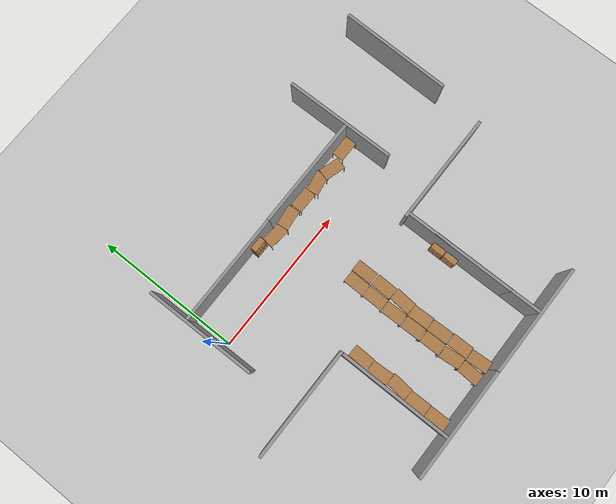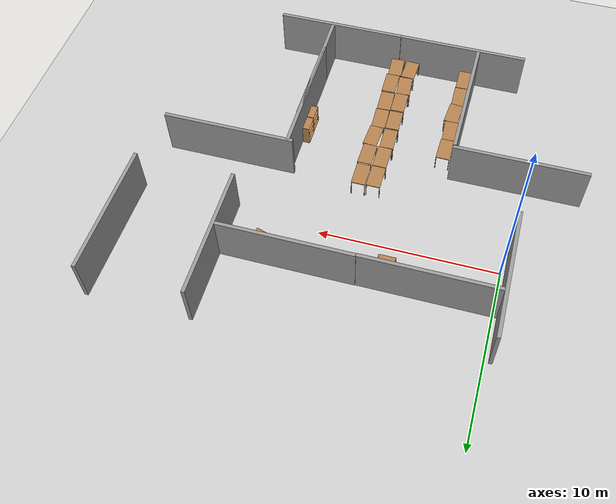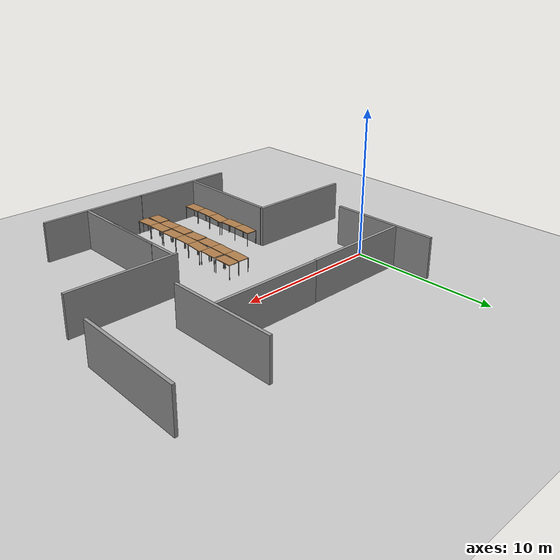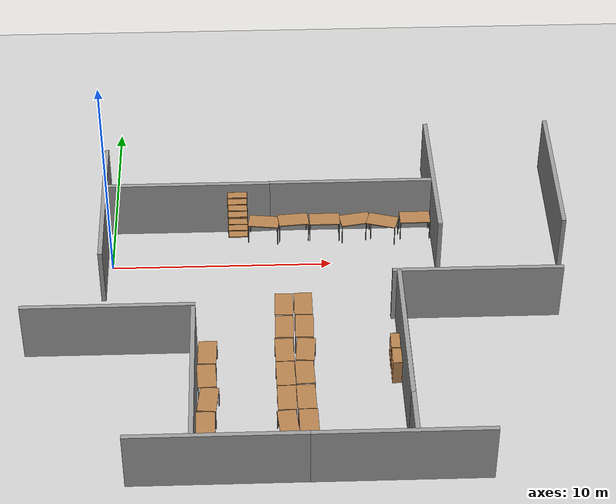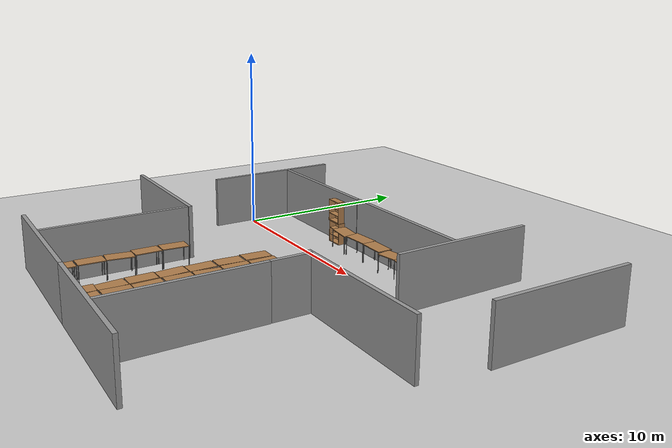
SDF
<sdf version="1.6">
 <world name="default">
  <light name="sun" type="directional">
   <pose>0 0 10 0 -0 0</pose>
   <diffuse>0.8 0.8 0.8 1</diffuse>
   <specular>0.1 0.1 0.1 1</specular>
   <attenuation>
    <range>1000</range>
    <constant>0.9</constant>
    <linear>0.01</linear>
    <quadratic>0.001</quadratic>
   </attenuation>
   <direction>-0.5 0.5 -1</direction>
  </light>
  <model name="ground_plane">
   <static>1</static>
   <link name="link">
    <collision name="collision">
     <geometry><plane><normal>0 0 1</normal><size>100 100</size></plane></geometry>
     <surface><friction><ode><mu>100</mu><mu2>50</mu2></ode></friction></surface>
    </collision>
    <visual name="visual">
     <cast_shadows>0</cast_shadows>
     <geometry><plane><normal>0 0 1</normal><size>100 100</size></plane></geometry>
     <material>
      <script><uri>file://media/materials/scripts/gazebo.material</uri><name>Gazebo/Grey</name></script>
     </material>
    </visual>
   </link>
  </model>
  <gravity>0 0 -9.8</gravity>
  <magnetic_field>6e-06 2.3e-05 -4.2e-05</magnetic_field>
  <atmosphere type="adiabatic"/>
  <physics name="default_physics" default="0" type="ode">
   <max_step_size>0.001</max_step_size>
   <real_time_factor>1</real_time_factor>
   <real_time_update_rate>1000</real_time_update_rate>
  </physics>
  <scene><ambient>0.4 0.4 0.4 1</ambient><background>0.7 0.7 0.7 1</background><shadows>1</shadows></scene>
  <spherical_coordinates>
   <surface_model>EARTH_WGS84</surface_model>
   <latitude_deg>0</latitude_deg>
   <longitude_deg>0</longitude_deg>
   <elevation>0</elevation>
   <heading_deg>0</heading_deg>
  </spherical_coordinates>
  <model name="grey_wall">
   <static>1</static>
   <link name="link">
    <pose>0 0 1.4 0 -0 0</pose>
    <collision name="collision"><geometry><box><size>7.5 0.2 2.8</size></box></geometry></collision>
    <visual name="visual">
     <cast_shadows>0</cast_shadows>
     <geometry><box><size>7.5 0.2 2.8</size></box></geometry>
     <material>
      <script>
       <uri>model://grey_wall/materials/scripts</uri>
       <uri>model://grey_wall/materials/textures</uri>
       <name>vrc/grey_wall</name>
      </script>
     </material>
    </visual>
   </link>
   <pose>3.5138 2.55142 0 0 -0 0</pose>
  </model>
  <model name="grey_wall_0">
   <static>1</static>
   <link name="link">
    <pose>0 0 1.4 0 -0 0</pose>
    <collision name="collision"><geometry><box><size>7.5 0.2 2.8</size></box></geometry></collision>
    <visual name="visual">
     <cast_shadows>0</cast_shadows>
     <geometry><box><size>7.5 0.2 2.8</size></box></geometry>
     <material>
      <script>
       <uri>model://grey_wall/materials/scripts</uri>
       <uri>model://grey_wall/materials/textures</uri>
       <name>vrc/grey_wall</name>
      </script>
     </material>
    </visual>
   </link>
   <pose>10.9804 2.57456 0 0 -0 0</pose>
  </model>
  <model name="grey_wall_1">
   <static>1</static>
   <link name="link">
    <pose>0 0 1.4 0 -0 0</pose>
    <collision name="collision"><geometry><box><size>7.5 0.2 2.8</size></box></geometry></collision>
    <visual name="visual">
     <cast_shadows>0</cast_shadows>
     <geometry><box><size>7.5 0.2 2.8</size></box></geometry>
     <material>
      <script>
       <uri>model://grey_wall/materials/scripts</uri>
       <uri>model://grey_wall/materials/textures</uri>
       <name>vrc/grey_wall</name>
      </script>
     </material>
    </visual>
   </link>
   <pose>14.8225 3.08441 0 0 0 -1.56171</pose>
  </model>
  <model name="grey_wall_2">
   <static>1</static>
   <link name="link">
    <pose>0 0 1.4 0 -0 0</pose>
    <collision name="collision"><geometry><box><size>7.5 0.2 2.8</size></box></geometry></collision>
    <visual name="visual">
     <cast_shadows>0</cast_shadows>
     <geometry><box><size>7.5 0.2 2.8</size></box></geometry>
     <material>
      <script>
       <uri>model://grey_wall/materials/scripts</uri>
       <uri>model://grey_wall/materials/textures</uri>
       <name>vrc/grey_wall</name>
      </script>
     </material>
    </visual>
   </link>
   <pose>-0.336177 1.50281 0 0 0 -1.56581</pose>
  </model>
  <model name="grey_wall_3">
   <static>1</static>
   <link name="link">
    <pose>0 0 1.4 0 -0 0</pose>
    <collision name="collision"><geometry><box><size>7.5 0.2 2.8</size></box></geometry></collision>
    <visual name="visual">
     <cast_shadows>0</cast_shadows>
     <geometry><box><size>7.5 0.2 2.8</size></box></geometry>
     <material>
      <script>
       <uri>model://grey_wall/materials/scripts</uri>
       <uri>model://grey_wall/materials/textures</uri>
       <name>vrc/grey_wall</name>
      </script>
     </material>
    </visual>
   </link>
   <pose>0.159876 -5.6283 0 0 -0 0</pose>
  </model>
  <model name="grey_wall_4">
   <static>1</static>
   <link name="link">
    <pose>0 0 1.4 0 -0 0</pose>
    <collision name="collision"><geometry><box><size>7.5 0.2 2.8</size></box></geometry></collision>
    <visual name="visual">
     <cast_shadows>0</cast_shadows>
     <geometry><box><size>7.5 0.2 2.8</size></box></geometry>
     <material>
      <script>
       <uri>model://grey_wall/materials/scripts</uri>
       <uri>model://grey_wall/materials/textures</uri>
       <name>vrc/grey_wall</name>
      </script>
     </material>
    </visual>
   </link>
   <pose>3.82152 -9.51174 0 0 0 -1.57182</pose>
  </model>
  <model name="grey_wall_5">
   <static>1</static>
   <link name="link">
    <pose>0 0 1.4 0 -0 0</pose>
    <collision name="collision"><geometry><box><size>7.5 0.2 2.8</size></box></geometry></collision>
    <visual name="visual">
     <cast_shadows>0</cast_shadows>
     <geometry><box><size>7.5 0.2 2.8</size></box></geometry>
     <material>
      <script>
       <uri>model://grey_wall/materials/scripts</uri>
       <uri>model://grey_wall/materials/textures</uri>
       <name>vrc/grey_wall</name>
      </script>
     </material>
    </visual>
   </link>
   <pose>16.2361 -3.7139 0 0 -0 0</pose>
  </model>
  <model name="grey_wall_6">
   <static>1</static>
   <link name="link">
    <pose>0 0 1.4 0 -0 0</pose>
    <collision name="collision"><geometry><box><size>7.5 0.2 2.8</size></box></geometry></collision>
    <visual name="visual">
     <cast_shadows>0</cast_shadows>
     <geometry><box><size>7.5 0.2 2.8</size></box></geometry>
     <material>
      <script>
       <uri>model://grey_wall/materials/scripts</uri>
       <uri>model://grey_wall/materials/textures</uri>
       <name>vrc/grey_wall</name>
      </script>
     </material>
    </visual>
   </link>
   <pose>12.8081 -9.51508 0 0 0 -1.5687</pose>
  </model>
  <model name="grey_wall_7">
   <static>1</static>
   <link name="link">
    <pose>0 0 1.4 0 -0 0</pose>
    <collision name="collision"><geometry><box><size>7.5 0.2 2.8</size></box></geometry></collision>
    <visual name="visual">
     <cast_shadows>0</cast_shadows>
     <geometry><box><size>7.5 0.2 2.8</size></box></geometry>
     <material>
      <script>
       <uri>model://grey_wall/materials/scripts</uri>
       <uri>model://grey_wall/materials/textures</uri>
       <name>vrc/grey_wall</name>
      </script>
     </material>
    </visual>
   </link>
   <pose>4.80097 -13.3442 0 0 -0 0</pose>
  </model>
  <model name="grey_wall_8">
   <static>1</static>
   <link name="link">
    <pose>0 0 1.4 0 -0 0</pose>
    <collision name="collision"><geometry><box><size>7.5 0.2 2.8</size></box></geometry></collision>
    <visual name="visual">
     <cast_shadows>0</cast_shadows>
     <geometry><box><size>7.5 0.2 2.8</size></box></geometry>
     <material>
      <script>
       <uri>model://grey_wall/materials/scripts</uri>
       <uri>model://grey_wall/materials/textures</uri>
       <name>vrc/grey_wall</name>
      </script>
     </material>
    </visual>
   </link>
   <pose>12.3131 -13.3481 0 0 -0 0</pose>
  </model>
  <model name="bookshelf">
   <static>1</static>
   <link name="link">
    <inertial><mass>1</mass></inertial>
    <collision name="back">
     <pose>0 0.005 0.6 0 -0 0</pose>
     <geometry><box><size>0.9 0.01 1.2</size></box></geometry>
    </collision>
    <visual name="visual1">
     <pose>0 0.005 0.6 0 -0 0</pose>
     <geometry><box><size>0.9 0.01 1.2</size></box></geometry>
     <material>
      <script><uri>file://media/materials/scripts/gazebo.material</uri><name>Gazebo/Wood</name></script>
     </material>
    </visual>
    <collision name="left_side">
     <pose>0.45 -0.195 0.6 0 -0 0</pose>
     <geometry><box><size>0.02 0.4 1.2</size></box></geometry>
    </collision>
    <visual name="visual2">
     <pose>0.45 -0.195 0.6 0 -0 0</pose>
     <geometry><box><size>0.02 0.4 1.2</size></box></geometry>
     <material>
      <script><uri>file://media/materials/scripts/gazebo.material</uri><name>Gazebo/Wood</name></script>
     </material>
    </visual>
    <collision name="right_side">
     <pose>-0.45 -0.195 0.6 0 -0 0</pose>
     <geometry><box><size>0.02 0.4 1.2</size></box></geometry>
    </collision>
    <visual name="visual3">
     <pose>-0.45 -0.195 0.6 0 -0 0</pose>
     <geometry><box><size>0.02 0.4 1.2</size></box></geometry>
     <material>
      <script><uri>file://media/materials/scripts/gazebo.material</uri><name>Gazebo/Wood</name></script>
     </material>
    </visual>
    <collision name="bottom">
     <pose>0 -0.195 0.03 0 -0 0</pose>
     <geometry><box><size>0.88 0.4 0.06</size></box></geometry>
    </collision>
    <visual name="visual4">
     <pose>0 -0.195 0.03 0 -0 0</pose>
     <geometry><box><size>0.88 0.4 0.06</size></box></geometry>
     <material>
      <script><uri>file://media/materials/scripts/gazebo.material</uri><name>Gazebo/Wood</name></script>
     </material>
    </visual>
    <collision name="top">
     <pose>0 -0.195 1.19 0 -0 0</pose>
     <geometry><box><size>0.88 0.4 0.02</size></box></geometry>
    </collision>
    <visual name="visual5">
     <pose>0 -0.195 1.19 0 -0 0</pose>
     <geometry><box><size>0.88 0.4 0.02</size></box></geometry>
     <material>
      <script><uri>file://media/materials/scripts/gazebo.material</uri><name>Gazebo/Wood</name></script>
     </material>
    </visual>
    <collision name="low_shelf">
     <pose>0 -0.195 0.43 0 -0 0</pose>
     <geometry><box><size>0.88 0.4 0.02</size></box></geometry>
    </collision>
    <visual name="visual6">
     <pose>0 -0.195 0.43 0 -0 0</pose>
     <geometry><box><size>0.88 0.4 0.02</size></box></geometry>
     <material>
      <script><uri>file://media/materials/scripts/gazebo.material</uri><name>Gazebo/Wood</name></script>
     </material>
    </visual>
    <collision name="high_shelf">
     <pose>0 -0.195 0.8 0 -0 0</pose>
     <geometry><box><size>0.88 0.4 0.02</size></box></geometry>
    </collision>
    <visual name="visual7">
     <pose>0 -0.195 0.8 0 -0 0</pose>
     <geometry><box><size>0.88 0.4 0.02</size></box></geometry>
     <material>
      <script><uri>file://media/materials/scripts/gazebo.material</uri><name>Gazebo/Wood</name></script>
     </material>
    </visual>
   </link>
   <pose>12.6657 -7.42335 0 0 0 -1.5772</pose>
  </model>
  <model name="grey_wall_9">
   <static>1</static>
   <link name="link">
    <pose>0 0 1.4 0 -0 0</pose>
    <collision name="collision"><geometry><box><size>7.5 0.2 2.8</size></box></geometry></collision>
    <visual name="visual">
     <cast_shadows>0</cast_shadows>
     <geometry><box><size>7.5 0.2 2.8</size></box></geometry>
     <material>
      <script>
       <uri>model://grey_wall/materials/scripts</uri>
       <uri>model://grey_wall/materials/textures</uri>
       <name>vrc/grey_wall</name>
      </script>
     </material>
    </visual>
   </link>
   <pose>20.4888 3.13835 0 0 -0 1.55576</pose>
  </model>
  <model name="table">
   <static>0</static>
   <link name="link">
    <collision name="surface">
     <pose>0 0 1 0 -0 0</pose>
     <geometry><box><size>1.5 0.8 0.03</size></box></geometry>
     <surface><friction><ode><mu>0.6</mu><mu2>0.6</mu2></ode></friction></surface>
    </collision>
    <visual name="visual1">
     <pose>0 0 1 0 -0 0</pose>
     <geometry><box><size>1.4 0.8 0.04</size></box></geometry>
     <material>
      <script><uri>file://media/materials/scripts/gazebo.material</uri><name>Gazebo/Wood</name></script>
     </material>
    </visual>
    <collision name="front_left_leg">
     <pose>0.68 0.38 0.5 0 -0 0</pose>
     <geometry><cylinder><radius>0.02</radius><length>1</length></cylinder></geometry>
    </collision>
    <visual name="front_left_leg">
     <pose>0.68 0.38 0.5 0 -0 0</pose>
     <geometry><cylinder><radius>0.02</radius><length>1</length></cylinder></geometry>
     <material>
      <script><uri>file://media/materials/scripts/gazebo.material</uri><name>Gazebo/Grey</name></script>
     </material>
    </visual>
    <collision name="front_right_leg">
     <pose>0.68 -0.38 0.5 0 -0 0</pose>
     <geometry><cylinder><radius>0.02</radius><length>1</length></cylinder></geometry>
    </collision>
    <visual name="front_right_leg">
     <pose>0.68 -0.38 0.5 0 -0 0</pose>
     <geometry><cylinder><radius>0.02</radius><length>1</length></cylinder></geometry>
     <material>
      <script><uri>file://media/materials/scripts/gazebo.material</uri><name>Gazebo/Grey</name></script>
     </material>
    </visual>
    <collision name="back_right_leg">
     <pose>-0.68 -0.38 0.5 0 -0 0</pose>
     <geometry><cylinder><radius>0.02</radius><length>1</length></cylinder></geometry>
    </collision>
    <visual name="back_right_leg">
     <pose>-0.68 -0.38 0.5 0 -0 0</pose>
     <geometry><cylinder><radius>0.02</radius><length>1</length></cylinder></geometry>
     <material>
      <script><uri>file://media/materials/scripts/gazebo.material</uri><name>Gazebo/Grey</name></script>
     </material>
    </visual>
    <collision name="back_left_leg">
     <pose>-0.68 0.38 0.5 0 -0 0</pose>
     <geometry><cylinder><radius>0.02</radius><length>1</length></cylinder></geometry>
    </collision>
    <visual name="back_left_leg">
     <pose>-0.68 0.38 0.5 0 -0 0</pose>
     <geometry><cylinder><radius>0.02</radius><length>1</length></cylinder></geometry>
     <material>
      <script><uri>file://media/materials/scripts/gazebo.material</uri><name>Gazebo/Grey</name></script>
     </material>
    </visual>
    <inertial>
     <inertia><ixx>1</ixx><ixy>0</ixy><ixz>0</ixz><iyy>1</iyy><iyz>0</iyz><izz>1</izz></inertia>
     <mass>1</mass>
    </inertial>
   </link>
   <pose>6.95725 1.92115 -0.00016 -1.1e-05 -7.6e-05 -0.121078</pose>
  </model>
  <model name="table_0">
   <static>0</static>
   <link name="link">
    <collision name="surface">
     <pose>0 0 1 0 -0 0</pose>
     <geometry><box><size>1.5 0.8 0.03</size></box></geometry>
     <surface><friction><ode><mu>0.6</mu><mu2>0.6</mu2></ode></friction></surface>
    </collision>
    <visual name="visual1">
     <pose>0 0 1 0 -0 0</pose>
     <geometry><box><size>1.4 0.8 0.04</size></box></geometry>
     <material>
      <script><uri>file://media/materials/scripts/gazebo.material</uri><name>Gazebo/Wood</name></script>
     </material>
    </visual>
    <collision name="front_left_leg">
     <pose>0.68 0.38 0.5 0 -0 0</pose>
     <geometry><cylinder><radius>0.02</radius><length>1</length></cylinder></geometry>
    </collision>
    <visual name="front_left_leg">
     <pose>0.68 0.38 0.5 0 -0 0</pose>
     <geometry><cylinder><radius>0.02</radius><length>1</length></cylinder></geometry>
     <material>
      <script><uri>file://media/materials/scripts/gazebo.material</uri><name>Gazebo/Grey</name></script>
     </material>
    </visual>
    <collision name="front_right_leg">
     <pose>0.68 -0.38 0.5 0 -0 0</pose>
     <geometry><cylinder><radius>0.02</radius><length>1</length></cylinder></geometry>
    </collision>
    <visual name="front_right_leg">
     <pose>0.68 -0.38 0.5 0 -0 0</pose>
     <geometry><cylinder><radius>0.02</radius><length>1</length></cylinder></geometry>
     <material>
      <script><uri>file://media/materials/scripts/gazebo.material</uri><name>Gazebo/Grey</name></script>
     </material>
    </visual>
    <collision name="back_right_leg">
     <pose>-0.68 -0.38 0.5 0 -0 0</pose>
     <geometry><cylinder><radius>0.02</radius><length>1</length></cylinder></geometry>
    </collision>
    <visual name="back_right_leg">
     <pose>-0.68 -0.38 0.5 0 -0 0</pose>
     <geometry><cylinder><radius>0.02</radius><length>1</length></cylinder></geometry>
     <material>
      <script><uri>file://media/materials/scripts/gazebo.material</uri><name>Gazebo/Grey</name></script>
     </material>
    </visual>
    <collision name="back_left_leg">
     <pose>-0.68 0.38 0.5 0 -0 0</pose>
     <geometry><cylinder><radius>0.02</radius><length>1</length></cylinder></geometry>
    </collision>
    <visual name="back_left_leg">
     <pose>-0.68 0.38 0.5 0 -0 0</pose>
     <geometry><cylinder><radius>0.02</radius><length>1</length></cylinder></geometry>
     <material>
      <script><uri>file://media/materials/scripts/gazebo.material</uri><name>Gazebo/Grey</name></script>
     </material>
    </visual>
    <inertial>
     <inertia><ixx>1</ixx><ixy>0</ixy><ixz>0</ixz><iyy>1</iyy><iyz>0</iyz><izz>1</izz></inertia>
     <mass>1</mass>
    </inertial>
   </link>
   <pose>8.29925 1.99529 0.017017 0.002681 0.022852 0.109343</pose>
  </model>
  <model name="table_1">
   <static>0</static>
   <link name="link">
    <collision name="surface">
     <pose>0 0 1 0 -0 0</pose>
     <geometry><box><size>1.5 0.8 0.03</size></box></geometry>
     <surface><friction><ode><mu>0.6</mu><mu2>0.6</mu2></ode></friction></surface>
    </collision>
    <visual name="visual1">
     <pose>0 0 1 0 -0 0</pose>
     <geometry><box><size>1.4 0.8 0.04</size></box></geometry>
     <material>
      <script><uri>file://media/materials/scripts/gazebo.material</uri><name>Gazebo/Wood</name></script>
     </material>
    </visual>
    <collision name="front_left_leg">
     <pose>0.68 0.38 0.5 0 -0 0</pose>
     <geometry><cylinder><radius>0.02</radius><length>1</length></cylinder></geometry>
    </collision>
    <visual name="front_left_leg">
     <pose>0.68 0.38 0.5 0 -0 0</pose>
     <geometry><cylinder><radius>0.02</radius><length>1</length></cylinder></geometry>
     <material>
      <script><uri>file://media/materials/scripts/gazebo.material</uri><name>Gazebo/Grey</name></script>
     </material>
    </visual>
    <collision name="front_right_leg">
     <pose>0.68 -0.38 0.5 0 -0 0</pose>
     <geometry><cylinder><radius>0.02</radius><length>1</length></cylinder></geometry>
    </collision>
    <visual name="front_right_leg">
     <pose>0.68 -0.38 0.5 0 -0 0</pose>
     <geometry><cylinder><radius>0.02</radius><length>1</length></cylinder></geometry>
     <material>
      <script><uri>file://media/materials/scripts/gazebo.material</uri><name>Gazebo/Grey</name></script>
     </material>
    </visual>
    <collision name="back_right_leg">
     <pose>-0.68 -0.38 0.5 0 -0 0</pose>
     <geometry><cylinder><radius>0.02</radius><length>1</length></cylinder></geometry>
    </collision>
    <visual name="back_right_leg">
     <pose>-0.68 -0.38 0.5 0 -0 0</pose>
     <geometry><cylinder><radius>0.02</radius><length>1</length></cylinder></geometry>
     <material>
      <script><uri>file://media/materials/scripts/gazebo.material</uri><name>Gazebo/Grey</name></script>
     </material>
    </visual>
    <collision name="back_left_leg">
     <pose>-0.68 0.38 0.5 0 -0 0</pose>
     <geometry><cylinder><radius>0.02</radius><length>1</length></cylinder></geometry>
    </collision>
    <visual name="back_left_leg">
     <pose>-0.68 0.38 0.5 0 -0 0</pose>
     <geometry><cylinder><radius>0.02</radius><length>1</length></cylinder></geometry>
     <material>
      <script><uri>file://media/materials/scripts/gazebo.material</uri><name>Gazebo/Grey</name></script>
     </material>
    </visual>
    <inertial>
     <inertia><ixx>1</ixx><ixy>0</ixy><ixz>0</ixz><iyy>1</iyy><iyz>0</iyz><izz>1</izz></inertia>
     <mass>1</mass>
    </inertial>
   </link>
   <pose>9.77254 1.97204 0.030307 -1.5e-05 0.000418 -0.008263</pose>
  </model>
  <model name="bookshelf_0">
   <static>1</static>
   <link name="link">
    <inertial><mass>1</mass></inertial>
    <collision name="back">
     <pose>0 0.005 0.6 0 -0 0</pose>
     <geometry><box><size>0.9 0.01 1.2</size></box></geometry>
    </collision>
    <visual name="visual1">
     <pose>0 0.005 0.6 0 -0 0</pose>
     <geometry><box><size>0.9 0.01 1.2</size></box></geometry>
     <material>
      <script><uri>file://media/materials/scripts/gazebo.material</uri><name>Gazebo/Wood</name></script>
     </material>
    </visual>
    <collision name="left_side">
     <pose>0.45 -0.195 0.6 0 -0 0</pose>
     <geometry><box><size>0.02 0.4 1.2</size></box></geometry>
    </collision>
    <visual name="visual2">
     <pose>0.45 -0.195 0.6 0 -0 0</pose>
     <geometry><box><size>0.02 0.4 1.2</size></box></geometry>
     <material>
      <script><uri>file://media/materials/scripts/gazebo.material</uri><name>Gazebo/Wood</name></script>
     </material>
    </visual>
    <collision name="right_side">
     <pose>-0.45 -0.195 0.6 0 -0 0</pose>
     <geometry><box><size>0.02 0.4 1.2</size></box></geometry>
    </collision>
    <visual name="visual3">
     <pose>-0.45 -0.195 0.6 0 -0 0</pose>
     <geometry><box><size>0.02 0.4 1.2</size></box></geometry>
     <material>
      <script><uri>file://media/materials/scripts/gazebo.material</uri><name>Gazebo/Wood</name></script>
     </material>
    </visual>
    <collision name="bottom">
     <pose>0 -0.195 0.03 0 -0 0</pose>
     <geometry><box><size>0.88 0.4 0.06</size></box></geometry>
    </collision>
    <visual name="visual4">
     <pose>0 -0.195 0.03 0 -0 0</pose>
     <geometry><box><size>0.88 0.4 0.06</size></box></geometry>
     <material>
      <script><uri>file://media/materials/scripts/gazebo.material</uri><name>Gazebo/Wood</name></script>
     </material>
    </visual>
    <collision name="top">
     <pose>0 -0.195 1.19 0 -0 0</pose>
     <geometry><box><size>0.88 0.4 0.02</size></box></geometry>
    </collision>
    <visual name="visual5">
     <pose>0 -0.195 1.19 0 -0 0</pose>
     <geometry><box><size>0.88 0.4 0.02</size></box></geometry>
     <material>
      <script><uri>file://media/materials/scripts/gazebo.material</uri><name>Gazebo/Wood</name></script>
     </material>
    </visual>
    <collision name="low_shelf">
     <pose>0 -0.195 0.43 0 -0 0</pose>
     <geometry><box><size>0.88 0.4 0.02</size></box></geometry>
    </collision>
    <visual name="visual6">
     <pose>0 -0.195 0.43 0 -0 0</pose>
     <geometry><box><size>0.88 0.4 0.02</size></box></geometry>
     <material>
      <script><uri>file://media/materials/scripts/gazebo.material</uri><name>Gazebo/Wood</name></script>
     </material>
    </visual>
    <collision name="high_shelf">
     <pose>0 -0.195 0.8 0 -0 0</pose>
     <geometry><box><size>0.88 0.4 0.02</size></box></geometry>
    </collision>
    <visual name="visual7">
     <pose>0 -0.195 0.8 0 -0 0</pose>
     <geometry><box><size>0.88 0.4 0.02</size></box></geometry>
     <material>
      <script><uri>file://media/materials/scripts/gazebo.material</uri><name>Gazebo/Wood</name></script>
     </material>
    </visual>
   </link>
   <pose>5.75252 2.40431 0 0 -0 0</pose>
  </model>
  <model name="bookshelf_1">
   <static>1</static>
   <link name="link">
    <inertial><mass>1</mass></inertial>
    <collision name="back">
     <pose>0 0.005 0.6 0 -0 0</pose>
     <geometry><box><size>0.9 0.01 1.2</size></box></geometry>
    </collision>
    <visual name="visual1">
     <pose>0 0.005 0.6 0 -0 0</pose>
     <geometry><box><size>0.9 0.01 1.2</size></box></geometry>
     <material>
      <script><uri>file://media/materials/scripts/gazebo.material</uri><name>Gazebo/Wood</name></script>
     </material>
    </visual>
    <collision name="left_side">
     <pose>0.45 -0.195 0.6 0 -0 0</pose>
     <geometry><box><size>0.02 0.4 1.2</size></box></geometry>
    </collision>
    <visual name="visual2">
     <pose>0.45 -0.195 0.6 0 -0 0</pose>
     <geometry><box><size>0.02 0.4 1.2</size></box></geometry>
     <material>
      <script><uri>file://media/materials/scripts/gazebo.material</uri><name>Gazebo/Wood</name></script>
     </material>
    </visual>
    <collision name="right_side">
     <pose>-0.45 -0.195 0.6 0 -0 0</pose>
     <geometry><box><size>0.02 0.4 1.2</size></box></geometry>
    </collision>
    <visual name="visual3">
     <pose>-0.45 -0.195 0.6 0 -0 0</pose>
     <geometry><box><size>0.02 0.4 1.2</size></box></geometry>
     <material>
      <script><uri>file://media/materials/scripts/gazebo.material</uri><name>Gazebo/Wood</name></script>
     </material>
    </visual>
    <collision name="bottom">
     <pose>0 -0.195 0.03 0 -0 0</pose>
     <geometry><box><size>0.88 0.4 0.06</size></box></geometry>
    </collision>
    <visual name="visual4">
     <pose>0 -0.195 0.03 0 -0 0</pose>
     <geometry><box><size>0.88 0.4 0.06</size></box></geometry>
     <material>
      <script><uri>file://media/materials/scripts/gazebo.material</uri><name>Gazebo/Wood</name></script>
     </material>
    </visual>
    <collision name="top">
     <pose>0 -0.195 1.19 0 -0 0</pose>
     <geometry><box><size>0.88 0.4 0.02</size></box></geometry>
    </collision>
    <visual name="visual5">
     <pose>0 -0.195 1.19 0 -0 0</pose>
     <geometry><box><size>0.88 0.4 0.02</size></box></geometry>
     <material>
      <script><uri>file://media/materials/scripts/gazebo.material</uri><name>Gazebo/Wood</name></script>
     </material>
    </visual>
    <collision name="low_shelf">
     <pose>0 -0.195 0.43 0 -0 0</pose>
     <geometry><box><size>0.88 0.4 0.02</size></box></geometry>
    </collision>
    <visual name="visual6">
     <pose>0 -0.195 0.43 0 -0 0</pose>
     <geometry><box><size>0.88 0.4 0.02</size></box></geometry>
     <material>
      <script><uri>file://media/materials/scripts/gazebo.material</uri><name>Gazebo/Wood</name></script>
     </material>
    </visual>
    <collision name="high_shelf">
     <pose>0 -0.195 0.8 0 -0 0</pose>
     <geometry><box><size>0.88 0.4 0.02</size></box></geometry>
    </collision>
    <visual name="visual7">
     <pose>0 -0.195 0.8 0 -0 0</pose>
     <geometry><box><size>0.88 0.4 0.02</size></box></geometry>
     <material>
      <script><uri>file://media/materials/scripts/gazebo.material</uri><name>Gazebo/Wood</name></script>
     </material>
    </visual>
   </link>
   <pose>5.74756 2.36627 1.21604 0 -0 0</pose>
  </model>
  <model name="table_2">
   <static>0</static>
   <link name="link">
    <collision name="surface">
     <pose>0 0 1 0 -0 0</pose>
     <geometry><box><size>1.5 0.8 0.03</size></box></geometry>
     <surface><friction><ode><mu>0.6</mu><mu2>0.6</mu2></ode></friction></surface>
    </collision>
    <visual name="visual1">
     <pose>0 0 1 0 -0 0</pose>
     <geometry><box><size>1.4 0.8 0.04</size></box></geometry>
     <material>
      <script><uri>file://media/materials/scripts/gazebo.material</uri><name>Gazebo/Wood</name></script>
     </material>
    </visual>
    <collision name="front_left_leg">
     <pose>0.68 0.38 0.5 0 -0 0</pose>
     <geometry><cylinder><radius>0.02</radius><length>1</length></cylinder></geometry>
    </collision>
    <visual name="front_left_leg">
     <pose>0.68 0.38 0.5 0 -0 0</pose>
     <geometry><cylinder><radius>0.02</radius><length>1</length></cylinder></geometry>
     <material>
      <script><uri>file://media/materials/scripts/gazebo.material</uri><name>Gazebo/Grey</name></script>
     </material>
    </visual>
    <collision name="front_right_leg">
     <pose>0.68 -0.38 0.5 0 -0 0</pose>
     <geometry><cylinder><radius>0.02</radius><length>1</length></cylinder></geometry>
    </collision>
    <visual name="front_right_leg">
     <pose>0.68 -0.38 0.5 0 -0 0</pose>
     <geometry><cylinder><radius>0.02</radius><length>1</length></cylinder></geometry>
     <material>
      <script><uri>file://media/materials/scripts/gazebo.material</uri><name>Gazebo/Grey</name></script>
     </material>
    </visual>
    <collision name="back_right_leg">
     <pose>-0.68 -0.38 0.5 0 -0 0</pose>
     <geometry><cylinder><radius>0.02</radius><length>1</length></cylinder></geometry>
    </collision>
    <visual name="back_right_leg">
     <pose>-0.68 -0.38 0.5 0 -0 0</pose>
     <geometry><cylinder><radius>0.02</radius><length>1</length></cylinder></geometry>
     <material>
      <script><uri>file://media/materials/scripts/gazebo.material</uri><name>Gazebo/Grey</name></script>
     </material>
    </visual>
    <collision name="back_left_leg">
     <pose>-0.68 0.38 0.5 0 -0 0</pose>
     <geometry><cylinder><radius>0.02</radius><length>1</length></cylinder></geometry>
    </collision>
    <visual name="back_left_leg">
     <pose>-0.68 0.38 0.5 0 -0 0</pose>
     <geometry><cylinder><radius>0.02</radius><length>1</length></cylinder></geometry>
     <material>
      <script><uri>file://media/materials/scripts/gazebo.material</uri><name>Gazebo/Grey</name></script>
     </material>
    </visual>
    <inertial>
     <inertia><ixx>1</ixx><ixy>0</ixy><ixz>0</ixz><iyy>1</iyy><iyz>0</iyz><izz>1</izz></inertia>
     <mass>1</mass>
    </inertial>
   </link>
   <pose>11.1931 1.9518 -5e-06 0 7e-06 0.172435</pose>
  </model>
  <model name="table_3">
   <static>0</static>
   <link name="link">
    <collision name="surface">
     <pose>0 0 1 0 -0 0</pose>
     <geometry><box><size>1.5 0.8 0.03</size></box></geometry>
     <surface><friction><ode><mu>0.6</mu><mu2>0.6</mu2></ode></friction></surface>
    </collision>
    <visual name="visual1">
     <pose>0 0 1 0 -0 0</pose>
     <geometry><box><size>1.4 0.8 0.04</size></box></geometry>
     <material>
      <script><uri>file://media/materials/scripts/gazebo.material</uri><name>Gazebo/Wood</name></script>
     </material>
    </visual>
    <collision name="front_left_leg">
     <pose>0.68 0.38 0.5 0 -0 0</pose>
     <geometry><cylinder><radius>0.02</radius><length>1</length></cylinder></geometry>
    </collision>
    <visual name="front_left_leg">
     <pose>0.68 0.38 0.5 0 -0 0</pose>
     <geometry><cylinder><radius>0.02</radius><length>1</length></cylinder></geometry>
     <material>
      <script><uri>file://media/materials/scripts/gazebo.material</uri><name>Gazebo/Grey</name></script>
     </material>
    </visual>
    <collision name="front_right_leg">
     <pose>0.68 -0.38 0.5 0 -0 0</pose>
     <geometry><cylinder><radius>0.02</radius><length>1</length></cylinder></geometry>
    </collision>
    <visual name="front_right_leg">
     <pose>0.68 -0.38 0.5 0 -0 0</pose>
     <geometry><cylinder><radius>0.02</radius><length>1</length></cylinder></geometry>
     <material>
      <script><uri>file://media/materials/scripts/gazebo.material</uri><name>Gazebo/Grey</name></script>
     </material>
    </visual>
    <collision name="back_right_leg">
     <pose>-0.68 -0.38 0.5 0 -0 0</pose>
     <geometry><cylinder><radius>0.02</radius><length>1</length></cylinder></geometry>
    </collision>
    <visual name="back_right_leg">
     <pose>-0.68 -0.38 0.5 0 -0 0</pose>
     <geometry><cylinder><radius>0.02</radius><length>1</length></cylinder></geometry>
     <material>
      <script><uri>file://media/materials/scripts/gazebo.material</uri><name>Gazebo/Grey</name></script>
     </material>
    </visual>
    <collision name="back_left_leg">
     <pose>-0.68 0.38 0.5 0 -0 0</pose>
     <geometry><cylinder><radius>0.02</radius><length>1</length></cylinder></geometry>
    </collision>
    <visual name="back_left_leg">
     <pose>-0.68 0.38 0.5 0 -0 0</pose>
     <geometry><cylinder><radius>0.02</radius><length>1</length></cylinder></geometry>
     <material>
      <script><uri>file://media/materials/scripts/gazebo.material</uri><name>Gazebo/Grey</name></script>
     </material>
    </visual>
    <inertial>
     <inertia><ixx>1</ixx><ixy>0</ixy><ixz>0</ixz><iyy>1</iyy><iyz>0</iyz><izz>1</izz></inertia>
     <mass>1</mass>
    </inertial>
   </link>
   <pose>12.4535 1.78657 0.029972 -0 4.3e-05 -0.283259</pose>
  </model>
  <model name="table_4">
   <static>0</static>
   <link name="link">
    <collision name="surface">
     <pose>0 0 1 0 -0 0</pose>
     <geometry><box><size>1.5 0.8 0.03</size></box></geometry>
     <surface><friction><ode><mu>0.6</mu><mu2>0.6</mu2></ode></friction></surface>
    </collision>
    <visual name="visual1">
     <pose>0 0 1 0 -0 0</pose>
     <geometry><box><size>1.4 0.8 0.04</size></box></geometry>
     <material>
      <script><uri>file://media/materials/scripts/gazebo.material</uri><name>Gazebo/Wood</name></script>
     </material>
    </visual>
    <collision name="front_left_leg">
     <pose>0.68 0.38 0.5 0 -0 0</pose>
     <geometry><cylinder><radius>0.02</radius><length>1</length></cylinder></geometry>
    </collision>
    <visual name="front_left_leg">
     <pose>0.68 0.38 0.5 0 -0 0</pose>
     <geometry><cylinder><radius>0.02</radius><length>1</length></cylinder></geometry>
     <material>
      <script><uri>file://media/materials/scripts/gazebo.material</uri><name>Gazebo/Grey</name></script>
     </material>
    </visual>
    <collision name="front_right_leg">
     <pose>0.68 -0.38 0.5 0 -0 0</pose>
     <geometry><cylinder><radius>0.02</radius><length>1</length></cylinder></geometry>
    </collision>
    <visual name="front_right_leg">
     <pose>0.68 -0.38 0.5 0 -0 0</pose>
     <geometry><cylinder><radius>0.02</radius><length>1</length></cylinder></geometry>
     <material>
      <script><uri>file://media/materials/scripts/gazebo.material</uri><name>Gazebo/Grey</name></script>
     </material>
    </visual>
    <collision name="back_right_leg">
     <pose>-0.68 -0.38 0.5 0 -0 0</pose>
     <geometry><cylinder><radius>0.02</radius><length>1</length></cylinder></geometry>
    </collision>
    <visual name="back_right_leg">
     <pose>-0.68 -0.38 0.5 0 -0 0</pose>
     <geometry><cylinder><radius>0.02</radius><length>1</length></cylinder></geometry>
     <material>
      <script><uri>file://media/materials/scripts/gazebo.material</uri><name>Gazebo/Grey</name></script>
     </material>
    </visual>
    <collision name="back_left_leg">
     <pose>-0.68 0.38 0.5 0 -0 0</pose>
     <geometry><cylinder><radius>0.02</radius><length>1</length></cylinder></geometry>
    </collision>
    <visual name="back_left_leg">
     <pose>-0.68 0.38 0.5 0 -0 0</pose>
     <geometry><cylinder><radius>0.02</radius><length>1</length></cylinder></geometry>
     <material>
      <script><uri>file://media/materials/scripts/gazebo.material</uri><name>Gazebo/Grey</name></script>
     </material>
    </visual>
    <inertial>
     <inertia><ixx>1</ixx><ixy>0</ixy><ixz>0</ixz><iyy>1</iyy><iyz>0</iyz><izz>1</izz></inertia>
     <mass>1</mass>
    </inertial>
   </link>
   <pose>13.9823 2.00803 -4.5e-05 4e-06 7e-06 0.009076</pose>
  </model>
  <model name="table_5">
   <static>0</static>
   <link name="link">
    <collision name="surface">
     <pose>0 0 1 0 -0 0</pose>
     <geometry><box><size>1.5 0.8 0.03</size></box></geometry>
     <surface><friction><ode><mu>0.6</mu><mu2>0.6</mu2></ode></friction></surface>
    </collision>
    <visual name="visual1">
     <pose>0 0 1 0 -0 0</pose>
     <geometry><box><size>1.4 0.8 0.04</size></box></geometry>
     <material>
      <script><uri>file://media/materials/scripts/gazebo.material</uri><name>Gazebo/Wood</name></script>
     </material>
    </visual>
    <collision name="front_left_leg">
     <pose>0.68 0.38 0.5 0 -0 0</pose>
     <geometry><cylinder><radius>0.02</radius><length>1</length></cylinder></geometry>
    </collision>
    <visual name="front_left_leg">
     <pose>0.68 0.38 0.5 0 -0 0</pose>
     <geometry><cylinder><radius>0.02</radius><length>1</length></cylinder></geometry>
     <material>
      <script><uri>file://media/materials/scripts/gazebo.material</uri><name>Gazebo/Grey</name></script>
     </material>
    </visual>
    <collision name="front_right_leg">
     <pose>0.68 -0.38 0.5 0 -0 0</pose>
     <geometry><cylinder><radius>0.02</radius><length>1</length></cylinder></geometry>
    </collision>
    <visual name="front_right_leg">
     <pose>0.68 -0.38 0.5 0 -0 0</pose>
     <geometry><cylinder><radius>0.02</radius><length>1</length></cylinder></geometry>
     <material>
      <script><uri>file://media/materials/scripts/gazebo.material</uri><name>Gazebo/Grey</name></script>
     </material>
    </visual>
    <collision name="back_right_leg">
     <pose>-0.68 -0.38 0.5 0 -0 0</pose>
     <geometry><cylinder><radius>0.02</radius><length>1</length></cylinder></geometry>
    </collision>
    <visual name="back_right_leg">
     <pose>-0.68 -0.38 0.5 0 -0 0</pose>
     <geometry><cylinder><radius>0.02</radius><length>1</length></cylinder></geometry>
     <material>
      <script><uri>file://media/materials/scripts/gazebo.material</uri><name>Gazebo/Grey</name></script>
     </material>
    </visual>
    <collision name="back_left_leg">
     <pose>-0.68 0.38 0.5 0 -0 0</pose>
     <geometry><cylinder><radius>0.02</radius><length>1</length></cylinder></geometry>
    </collision>
    <visual name="back_left_leg">
     <pose>-0.68 0.38 0.5 0 -0 0</pose>
     <geometry><cylinder><radius>0.02</radius><length>1</length></cylinder></geometry>
     <material>
      <script><uri>file://media/materials/scripts/gazebo.material</uri><name>Gazebo/Grey</name></script>
     </material>
    </visual>
    <inertial>
     <inertia><ixx>1</ixx><ixy>0</ixy><ixz>0</ixz><iyy>1</iyy><iyz>0</iyz><izz>1</izz></inertia>
     <mass>1</mass>
    </inertial>
   </link>
   <pose>8.56264 -12.4509 0.014876 -0.001011 0.020718 -1.51118</pose>
  </model>
  <model name="table_5_clone">
   <static>0</static>
   <link name="link">
    <collision name="surface">
     <pose>0 0 1 0 -0 0</pose>
     <geometry><box><size>1.5 0.8 0.03</size></box></geometry>
     <surface><friction><ode><mu>0.6</mu><mu2>0.6</mu2></ode></friction></surface>
    </collision>
    <visual name="visual1">
     <pose>0 0 1 0 -0 0</pose>
     <geometry><box><size>1.4 0.8 0.04</size></box></geometry>
     <material>
      <script><uri>file://media/materials/scripts/gazebo.material</uri><name>Gazebo/Wood</name></script>
     </material>
    </visual>
    <collision name="front_left_leg">
     <pose>0.68 0.38 0.5 0 -0 0</pose>
     <geometry><cylinder><radius>0.02</radius><length>1</length></cylinder></geometry>
    </collision>
    <visual name="front_left_leg">
     <pose>0.68 0.38 0.5 0 -0 0</pose>
     <geometry><cylinder><radius>0.02</radius><length>1</length></cylinder></geometry>
     <material>
      <script><uri>file://media/materials/scripts/gazebo.material</uri><name>Gazebo/Grey</name></script>
     </material>
    </visual>
    <collision name="front_right_leg">
     <pose>0.68 -0.38 0.5 0 -0 0</pose>
     <geometry><cylinder><radius>0.02</radius><length>1</length></cylinder></geometry>
    </collision>
    <visual name="front_right_leg">
     <pose>0.68 -0.38 0.5 0 -0 0</pose>
     <geometry><cylinder><radius>0.02</radius><length>1</length></cylinder></geometry>
     <material>
      <script><uri>file://media/materials/scripts/gazebo.material</uri><name>Gazebo/Grey</name></script>
     </material>
    </visual>
    <collision name="back_right_leg">
     <pose>-0.68 -0.38 0.5 0 -0 0</pose>
     <geometry><cylinder><radius>0.02</radius><length>1</length></cylinder></geometry>
    </collision>
    <visual name="back_right_leg">
     <pose>-0.68 -0.38 0.5 0 -0 0</pose>
     <geometry><cylinder><radius>0.02</radius><length>1</length></cylinder></geometry>
     <material>
      <script><uri>file://media/materials/scripts/gazebo.material</uri><name>Gazebo/Grey</name></script>
     </material>
    </visual>
    <collision name="back_left_leg">
     <pose>-0.68 0.38 0.5 0 -0 0</pose>
     <geometry><cylinder><radius>0.02</radius><length>1</length></cylinder></geometry>
    </collision>
    <visual name="back_left_leg">
     <pose>-0.68 0.38 0.5 0 -0 0</pose>
     <geometry><cylinder><radius>0.02</radius><length>1</length></cylinder></geometry>
     <material>
      <script><uri>file://media/materials/scripts/gazebo.material</uri><name>Gazebo/Grey</name></script>
     </material>
    </visual>
    <inertial>
     <inertia><ixx>1</ixx><ixy>0</ixy><ixz>0</ixz><iyy>1</iyy><iyz>0</iyz><izz>1</izz></inertia>
     <mass>1</mass>
    </inertial>
   </link>
   <pose>8.59029 -11.0553 0.045945 -3.2e-05 -0.021002 -1.55607</pose>
  </model>
  <model name="table_5_clone_0">
   <static>0</static>
   <link name="link">
    <collision name="surface">
     <pose>0 0 1 0 -0 0</pose>
     <geometry><box><size>1.5 0.8 0.03</size></box></geometry>
     <surface><friction><ode><mu>0.6</mu><mu2>0.6</mu2></ode></friction></surface>
    </collision>
    <visual name="visual1">
     <pose>0 0 1 0 -0 0</pose>
     <geometry><box><size>1.4 0.8 0.04</size></box></geometry>
     <material>
      <script><uri>file://media/materials/scripts/gazebo.material</uri><name>Gazebo/Wood</name></script>
     </material>
    </visual>
    <collision name="front_left_leg">
     <pose>0.68 0.38 0.5 0 -0 0</pose>
     <geometry><cylinder><radius>0.02</radius><length>1</length></cylinder></geometry>
    </collision>
    <visual name="front_left_leg">
     <pose>0.68 0.38 0.5 0 -0 0</pose>
     <geometry><cylinder><radius>0.02</radius><length>1</length></cylinder></geometry>
     <material>
      <script><uri>file://media/materials/scripts/gazebo.material</uri><name>Gazebo/Grey</name></script>
     </material>
    </visual>
    <collision name="front_right_leg">
     <pose>0.68 -0.38 0.5 0 -0 0</pose>
     <geometry><cylinder><radius>0.02</radius><length>1</length></cylinder></geometry>
    </collision>
    <visual name="front_right_leg">
     <pose>0.68 -0.38 0.5 0 -0 0</pose>
     <geometry><cylinder><radius>0.02</radius><length>1</length></cylinder></geometry>
     <material>
      <script><uri>file://media/materials/scripts/gazebo.material</uri><name>Gazebo/Grey</name></script>
     </material>
    </visual>
    <collision name="back_right_leg">
     <pose>-0.68 -0.38 0.5 0 -0 0</pose>
     <geometry><cylinder><radius>0.02</radius><length>1</length></cylinder></geometry>
    </collision>
    <visual name="back_right_leg">
     <pose>-0.68 -0.38 0.5 0 -0 0</pose>
     <geometry><cylinder><radius>0.02</radius><length>1</length></cylinder></geometry>
     <material>
      <script><uri>file://media/materials/scripts/gazebo.material</uri><name>Gazebo/Grey</name></script>
     </material>
    </visual>
    <collision name="back_left_leg">
     <pose>-0.68 0.38 0.5 0 -0 0</pose>
     <geometry><cylinder><radius>0.02</radius><length>1</length></cylinder></geometry>
    </collision>
    <visual name="back_left_leg">
     <pose>-0.68 0.38 0.5 0 -0 0</pose>
     <geometry><cylinder><radius>0.02</radius><length>1</length></cylinder></geometry>
     <material>
      <script><uri>file://media/materials/scripts/gazebo.material</uri><name>Gazebo/Grey</name></script>
     </material>
    </visual>
    <inertial>
     <inertia><ixx>1</ixx><ixy>0</ixy><ixz>0</ixz><iyy>1</iyy><iyz>0</iyz><izz>1</izz></inertia>
     <mass>1</mass>
    </inertial>
   </link>
   <pose>8.5353 -9.58081 -0.000122 -1.9e-05 3.4e-05 -1.5427</pose>
  </model>
  <model name="table_5_clone_1">
   <static>0</static>
   <link name="link">
    <collision name="surface">
     <pose>0 0 1 0 -0 0</pose>
     <geometry><box><size>1.5 0.8 0.03</size></box></geometry>
     <surface><friction><ode><mu>0.6</mu><mu2>0.6</mu2></ode></friction></surface>
    </collision>
    <visual name="visual1">
     <pose>0 0 1 0 -0 0</pose>
     <geometry><box><size>1.4 0.8 0.04</size></box></geometry>
     <material>
      <script><uri>file://media/materials/scripts/gazebo.material</uri><name>Gazebo/Wood</name></script>
     </material>
    </visual>
    <collision name="front_left_leg">
     <pose>0.68 0.38 0.5 0 -0 0</pose>
     <geometry><cylinder><radius>0.02</radius><length>1</length></cylinder></geometry>
    </collision>
    <visual name="front_left_leg">
     <pose>0.68 0.38 0.5 0 -0 0</pose>
     <geometry><cylinder><radius>0.02</radius><length>1</length></cylinder></geometry>
     <material>
      <script><uri>file://media/materials/scripts/gazebo.material</uri><name>Gazebo/Grey</name></script>
     </material>
    </visual>
    <collision name="front_right_leg">
     <pose>0.68 -0.38 0.5 0 -0 0</pose>
     <geometry><cylinder><radius>0.02</radius><length>1</length></cylinder></geometry>
    </collision>
    <visual name="front_right_leg">
     <pose>0.68 -0.38 0.5 0 -0 0</pose>
     <geometry><cylinder><radius>0.02</radius><length>1</length></cylinder></geometry>
     <material>
      <script><uri>file://media/materials/scripts/gazebo.material</uri><name>Gazebo/Grey</name></script>
     </material>
    </visual>
    <collision name="back_right_leg">
     <pose>-0.68 -0.38 0.5 0 -0 0</pose>
     <geometry><cylinder><radius>0.02</radius><length>1</length></cylinder></geometry>
    </collision>
    <visual name="back_right_leg">
     <pose>-0.68 -0.38 0.5 0 -0 0</pose>
     <geometry><cylinder><radius>0.02</radius><length>1</length></cylinder></geometry>
     <material>
      <script><uri>file://media/materials/scripts/gazebo.material</uri><name>Gazebo/Grey</name></script>
     </material>
    </visual>
    <collision name="back_left_leg">
     <pose>-0.68 0.38 0.5 0 -0 0</pose>
     <geometry><cylinder><radius>0.02</radius><length>1</length></cylinder></geometry>
    </collision>
    <visual name="back_left_leg">
     <pose>-0.68 0.38 0.5 0 -0 0</pose>
     <geometry><cylinder><radius>0.02</radius><length>1</length></cylinder></geometry>
     <material>
      <script><uri>file://media/materials/scripts/gazebo.material</uri><name>Gazebo/Grey</name></script>
     </material>
    </visual>
    <inertial>
     <inertia><ixx>1</ixx><ixy>0</ixy><ixz>0</ixz><iyy>1</iyy><iyz>0</iyz><izz>1</izz></inertia>
     <mass>1</mass>
    </inertial>
   </link>
   <pose>8.52122 -8.15174 0.015004 -9e-06 -0.021522 -1.5436</pose>
  </model>
  <model name="table_5_clone_2">
   <static>0</static>
   <link name="link">
    <collision name="surface">
     <pose>0 0 1 0 -0 0</pose>
     <geometry><box><size>1.5 0.8 0.03</size></box></geometry>
     <surface><friction><ode><mu>0.6</mu><mu2>0.6</mu2></ode></friction></surface>
    </collision>
    <visual name="visual1">
     <pose>0 0 1 0 -0 0</pose>
     <geometry><box><size>1.4 0.8 0.04</size></box></geometry>
     <material>
      <script><uri>file://media/materials/scripts/gazebo.material</uri><name>Gazebo/Wood</name></script>
     </material>
    </visual>
    <collision name="front_left_leg">
     <pose>0.68 0.38 0.5 0 -0 0</pose>
     <geometry><cylinder><radius>0.02</radius><length>1</length></cylinder></geometry>
    </collision>
    <visual name="front_left_leg">
     <pose>0.68 0.38 0.5 0 -0 0</pose>
     <geometry><cylinder><radius>0.02</radius><length>1</length></cylinder></geometry>
     <material>
      <script><uri>file://media/materials/scripts/gazebo.material</uri><name>Gazebo/Grey</name></script>
     </material>
    </visual>
    <collision name="front_right_leg">
     <pose>0.68 -0.38 0.5 0 -0 0</pose>
     <geometry><cylinder><radius>0.02</radius><length>1</length></cylinder></geometry>
    </collision>
    <visual name="front_right_leg">
     <pose>0.68 -0.38 0.5 0 -0 0</pose>
     <geometry><cylinder><radius>0.02</radius><length>1</length></cylinder></geometry>
     <material>
      <script><uri>file://media/materials/scripts/gazebo.material</uri><name>Gazebo/Grey</name></script>
     </material>
    </visual>
    <collision name="back_right_leg">
     <pose>-0.68 -0.38 0.5 0 -0 0</pose>
     <geometry><cylinder><radius>0.02</radius><length>1</length></cylinder></geometry>
    </collision>
    <visual name="back_right_leg">
     <pose>-0.68 -0.38 0.5 0 -0 0</pose>
     <geometry><cylinder><radius>0.02</radius><length>1</length></cylinder></geometry>
     <material>
      <script><uri>file://media/materials/scripts/gazebo.material</uri><name>Gazebo/Grey</name></script>
     </material>
    </visual>
    <collision name="back_left_leg">
     <pose>-0.68 0.38 0.5 0 -0 0</pose>
     <geometry><cylinder><radius>0.02</radius><length>1</length></cylinder></geometry>
    </collision>
    <visual name="back_left_leg">
     <pose>-0.68 0.38 0.5 0 -0 0</pose>
     <geometry><cylinder><radius>0.02</radius><length>1</length></cylinder></geometry>
     <material>
      <script><uri>file://media/materials/scripts/gazebo.material</uri><name>Gazebo/Grey</name></script>
     </material>
    </visual>
    <inertial>
     <inertia><ixx>1</ixx><ixy>0</ixy><ixz>0</ixz><iyy>1</iyy><iyz>0</iyz><izz>1</izz></inertia>
     <mass>1</mass>
    </inertial>
   </link>
   <pose>8.5981 -6.74409 0.015299 -0 -0.021857 -1.65205</pose>
  </model>
  <model name="table_5_clone_3">
   <static>0</static>
   <link name="link">
    <collision name="surface">
     <pose>0 0 1 0 -0 0</pose>
     <geometry><box><size>1.5 0.8 0.03</size></box></geometry>
     <surface><friction><ode><mu>0.6</mu><mu2>0.6</mu2></ode></friction></surface>
    </collision>
    <visual name="visual1">
     <pose>0 0 1 0 -0 0</pose>
     <geometry><box><size>1.4 0.8 0.04</size></box></geometry>
     <material>
      <script><uri>file://media/materials/scripts/gazebo.material</uri><name>Gazebo/Wood</name></script>
     </material>
    </visual>
    <collision name="front_left_leg">
     <pose>0.68 0.38 0.5 0 -0 0</pose>
     <geometry><cylinder><radius>0.02</radius><length>1</length></cylinder></geometry>
    </collision>
    <visual name="front_left_leg">
     <pose>0.68 0.38 0.5 0 -0 0</pose>
     <geometry><cylinder><radius>0.02</radius><length>1</length></cylinder></geometry>
     <material>
      <script><uri>file://media/materials/scripts/gazebo.material</uri><name>Gazebo/Grey</name></script>
     </material>
    </visual>
    <collision name="front_right_leg">
     <pose>0.68 -0.38 0.5 0 -0 0</pose>
     <geometry><cylinder><radius>0.02</radius><length>1</length></cylinder></geometry>
    </collision>
    <visual name="front_right_leg">
     <pose>0.68 -0.38 0.5 0 -0 0</pose>
     <geometry><cylinder><radius>0.02</radius><length>1</length></cylinder></geometry>
     <material>
      <script><uri>file://media/materials/scripts/gazebo.material</uri><name>Gazebo/Grey</name></script>
     </material>
    </visual>
    <collision name="back_right_leg">
     <pose>-0.68 -0.38 0.5 0 -0 0</pose>
     <geometry><cylinder><radius>0.02</radius><length>1</length></cylinder></geometry>
    </collision>
    <visual name="back_right_leg">
     <pose>-0.68 -0.38 0.5 0 -0 0</pose>
     <geometry><cylinder><radius>0.02</radius><length>1</length></cylinder></geometry>
     <material>
      <script><uri>file://media/materials/scripts/gazebo.material</uri><name>Gazebo/Grey</name></script>
     </material>
    </visual>
    <collision name="back_left_leg">
     <pose>-0.68 0.38 0.5 0 -0 0</pose>
     <geometry><cylinder><radius>0.02</radius><length>1</length></cylinder></geometry>
    </collision>
    <visual name="back_left_leg">
     <pose>-0.68 0.38 0.5 0 -0 0</pose>
     <geometry><cylinder><radius>0.02</radius><length>1</length></cylinder></geometry>
     <material>
      <script><uri>file://media/materials/scripts/gazebo.material</uri><name>Gazebo/Grey</name></script>
     </material>
    </visual>
    <inertial>
     <inertia><ixx>1</ixx><ixy>0</ixy><ixz>0</ixz><iyy>1</iyy><iyz>0</iyz><izz>1</izz></inertia>
     <mass>1</mass>
    </inertial>
   </link>
   <pose>7.68511 -6.73105 -1.7e-05 -1e-06 -5e-06 -1.54956</pose>
  </model>
  <model name="table_5_clone_4">
   <static>0</static>
   <link name="link">
    <collision name="surface">
     <pose>0 0 1 0 -0 0</pose>
     <geometry><box><size>1.5 0.8 0.03</size></box></geometry>
     <surface><friction><ode><mu>0.6</mu><mu2>0.6</mu2></ode></friction></surface>
    </collision>
    <visual name="visual1">
     <pose>0 0 1 0 -0 0</pose>
     <geometry><box><size>1.4 0.8 0.04</size></box></geometry>
     <material>
      <script><uri>file://media/materials/scripts/gazebo.material</uri><name>Gazebo/Wood</name></script>
     </material>
    </visual>
    <collision name="front_left_leg">
     <pose>0.68 0.38 0.5 0 -0 0</pose>
     <geometry><cylinder><radius>0.02</radius><length>1</length></cylinder></geometry>
    </collision>
    <visual name="front_left_leg">
     <pose>0.68 0.38 0.5 0 -0 0</pose>
     <geometry><cylinder><radius>0.02</radius><length>1</length></cylinder></geometry>
     <material>
      <script><uri>file://media/materials/scripts/gazebo.material</uri><name>Gazebo/Grey</name></script>
     </material>
    </visual>
    <collision name="front_right_leg">
     <pose>0.68 -0.38 0.5 0 -0 0</pose>
     <geometry><cylinder><radius>0.02</radius><length>1</length></cylinder></geometry>
    </collision>
    <visual name="front_right_leg">
     <pose>0.68 -0.38 0.5 0 -0 0</pose>
     <geometry><cylinder><radius>0.02</radius><length>1</length></cylinder></geometry>
     <material>
      <script><uri>file://media/materials/scripts/gazebo.material</uri><name>Gazebo/Grey</name></script>
     </material>
    </visual>
    <collision name="back_right_leg">
     <pose>-0.68 -0.38 0.5 0 -0 0</pose>
     <geometry><cylinder><radius>0.02</radius><length>1</length></cylinder></geometry>
    </collision>
    <visual name="back_right_leg">
     <pose>-0.68 -0.38 0.5 0 -0 0</pose>
     <geometry><cylinder><radius>0.02</radius><length>1</length></cylinder></geometry>
     <material>
      <script><uri>file://media/materials/scripts/gazebo.material</uri><name>Gazebo/Grey</name></script>
     </material>
    </visual>
    <collision name="back_left_leg">
     <pose>-0.68 0.38 0.5 0 -0 0</pose>
     <geometry><cylinder><radius>0.02</radius><length>1</length></cylinder></geometry>
    </collision>
    <visual name="back_left_leg">
     <pose>-0.68 0.38 0.5 0 -0 0</pose>
     <geometry><cylinder><radius>0.02</radius><length>1</length></cylinder></geometry>
     <material>
      <script><uri>file://media/materials/scripts/gazebo.material</uri><name>Gazebo/Grey</name></script>
     </material>
    </visual>
    <inertial>
     <inertia><ixx>1</ixx><ixy>0</ixy><ixz>0</ixz><iyy>1</iyy><iyz>0</iyz><izz>1</izz></inertia>
     <mass>1</mass>
    </inertial>
   </link>
   <pose>7.69986 -8.16028 0.015103 0 0.021577 -1.54957</pose>
  </model>
  <model name="table_5_clone_5">
   <static>0</static>
   <link name="link">
    <collision name="surface">
     <pose>0 0 1 0 -0 0</pose>
     <geometry><box><size>1.5 0.8 0.03</size></box></geometry>
     <surface><friction><ode><mu>0.6</mu><mu2>0.6</mu2></ode></friction></surface>
    </collision>
    <visual name="visual1">
     <pose>0 0 1 0 -0 0</pose>
     <geometry><box><size>1.4 0.8 0.04</size></box></geometry>
     <material>
      <script><uri>file://media/materials/scripts/gazebo.material</uri><name>Gazebo/Wood</name></script>
     </material>
    </visual>
    <collision name="front_left_leg">
     <pose>0.68 0.38 0.5 0 -0 0</pose>
     <geometry><cylinder><radius>0.02</radius><length>1</length></cylinder></geometry>
    </collision>
    <visual name="front_left_leg">
     <pose>0.68 0.38 0.5 0 -0 0</pose>
     <geometry><cylinder><radius>0.02</radius><length>1</length></cylinder></geometry>
     <material>
      <script><uri>file://media/materials/scripts/gazebo.material</uri><name>Gazebo/Grey</name></script>
     </material>
    </visual>
    <collision name="front_right_leg">
     <pose>0.68 -0.38 0.5 0 -0 0</pose>
     <geometry><cylinder><radius>0.02</radius><length>1</length></cylinder></geometry>
    </collision>
    <visual name="front_right_leg">
     <pose>0.68 -0.38 0.5 0 -0 0</pose>
     <geometry><cylinder><radius>0.02</radius><length>1</length></cylinder></geometry>
     <material>
      <script><uri>file://media/materials/scripts/gazebo.material</uri><name>Gazebo/Grey</name></script>
     </material>
    </visual>
    <collision name="back_right_leg">
     <pose>-0.68 -0.38 0.5 0 -0 0</pose>
     <geometry><cylinder><radius>0.02</radius><length>1</length></cylinder></geometry>
    </collision>
    <visual name="back_right_leg">
     <pose>-0.68 -0.38 0.5 0 -0 0</pose>
     <geometry><cylinder><radius>0.02</radius><length>1</length></cylinder></geometry>
     <material>
      <script><uri>file://media/materials/scripts/gazebo.material</uri><name>Gazebo/Grey</name></script>
     </material>
    </visual>
    <collision name="back_left_leg">
     <pose>-0.68 0.38 0.5 0 -0 0</pose>
     <geometry><cylinder><radius>0.02</radius><length>1</length></cylinder></geometry>
    </collision>
    <visual name="back_left_leg">
     <pose>-0.68 0.38 0.5 0 -0 0</pose>
     <geometry><cylinder><radius>0.02</radius><length>1</length></cylinder></geometry>
     <material>
      <script><uri>file://media/materials/scripts/gazebo.material</uri><name>Gazebo/Grey</name></script>
     </material>
    </visual>
    <inertial>
     <inertia><ixx>1</ixx><ixy>0</ixy><ixz>0</ixz><iyy>1</iyy><iyz>0</iyz><izz>1</izz></inertia>
     <mass>1</mass>
    </inertial>
   </link>
   <pose>7.68689 -12.4351 0.016255 -9e-06 0.023245 -1.61942</pose>
  </model>
  <model name="table_5_clone_6">
   <static>0</static>
   <link name="link">
    <collision name="surface">
     <pose>0 0 1 0 -0 0</pose>
     <geometry><box><size>1.5 0.8 0.03</size></box></geometry>
     <surface><friction><ode><mu>0.6</mu><mu2>0.6</mu2></ode></friction></surface>
    </collision>
    <visual name="visual1">
     <pose>0 0 1 0 -0 0</pose>
     <geometry><box><size>1.4 0.8 0.04</size></box></geometry>
     <material>
      <script><uri>file://media/materials/scripts/gazebo.material</uri><name>Gazebo/Wood</name></script>
     </material>
    </visual>
    <collision name="front_left_leg">
     <pose>0.68 0.38 0.5 0 -0 0</pose>
     <geometry><cylinder><radius>0.02</radius><length>1</length></cylinder></geometry>
    </collision>
    <visual name="front_left_leg">
     <pose>0.68 0.38 0.5 0 -0 0</pose>
     <geometry><cylinder><radius>0.02</radius><length>1</length></cylinder></geometry>
     <material>
      <script><uri>file://media/materials/scripts/gazebo.material</uri><name>Gazebo/Grey</name></script>
     </material>
    </visual>
    <collision name="front_right_leg">
     <pose>0.68 -0.38 0.5 0 -0 0</pose>
     <geometry><cylinder><radius>0.02</radius><length>1</length></cylinder></geometry>
    </collision>
    <visual name="front_right_leg">
     <pose>0.68 -0.38 0.5 0 -0 0</pose>
     <geometry><cylinder><radius>0.02</radius><length>1</length></cylinder></geometry>
     <material>
      <script><uri>file://media/materials/scripts/gazebo.material</uri><name>Gazebo/Grey</name></script>
     </material>
    </visual>
    <collision name="back_right_leg">
     <pose>-0.68 -0.38 0.5 0 -0 0</pose>
     <geometry><cylinder><radius>0.02</radius><length>1</length></cylinder></geometry>
    </collision>
    <visual name="back_right_leg">
     <pose>-0.68 -0.38 0.5 0 -0 0</pose>
     <geometry><cylinder><radius>0.02</radius><length>1</length></cylinder></geometry>
     <material>
      <script><uri>file://media/materials/scripts/gazebo.material</uri><name>Gazebo/Grey</name></script>
     </material>
    </visual>
    <collision name="back_left_leg">
     <pose>-0.68 0.38 0.5 0 -0 0</pose>
     <geometry><cylinder><radius>0.02</radius><length>1</length></cylinder></geometry>
    </collision>
    <visual name="back_left_leg">
     <pose>-0.68 0.38 0.5 0 -0 0</pose>
     <geometry><cylinder><radius>0.02</radius><length>1</length></cylinder></geometry>
     <material>
      <script><uri>file://media/materials/scripts/gazebo.material</uri><name>Gazebo/Grey</name></script>
     </material>
    </visual>
    <inertial>
     <inertia><ixx>1</ixx><ixy>0</ixy><ixz>0</ixz><iyy>1</iyy><iyz>0</iyz><izz>1</izz></inertia>
     <mass>1</mass>
    </inertial>
   </link>
   <pose>7.73634 -11.057 -1.3e-05 -2e-06 -5e-06 -1.47784</pose>
  </model>
  <model name="table_5_clone_7">
   <static>0</static>
   <link name="link">
    <collision name="surface">
     <pose>0 0 1 0 -0 0</pose>
     <geometry><box><size>1.5 0.8 0.03</size></box></geometry>
     <surface><friction><ode><mu>0.6</mu><mu2>0.6</mu2></ode></friction></surface>
    </collision>
    <visual name="visual1">
     <pose>0 0 1 0 -0 0</pose>
     <geometry><box><size>1.4 0.8 0.04</size></box></geometry>
     <material>
      <script><uri>file://media/materials/scripts/gazebo.material</uri><name>Gazebo/Wood</name></script>
     </material>
    </visual>
    <collision name="front_left_leg">
     <pose>0.68 0.38 0.5 0 -0 0</pose>
     <geometry><cylinder><radius>0.02</radius><length>1</length></cylinder></geometry>
    </collision>
    <visual name="front_left_leg">
     <pose>0.68 0.38 0.5 0 -0 0</pose>
     <geometry><cylinder><radius>0.02</radius><length>1</length></cylinder></geometry>
     <material>
      <script><uri>file://media/materials/scripts/gazebo.material</uri><name>Gazebo/Grey</name></script>
     </material>
    </visual>
    <collision name="front_right_leg">
     <pose>0.68 -0.38 0.5 0 -0 0</pose>
     <geometry><cylinder><radius>0.02</radius><length>1</length></cylinder></geometry>
    </collision>
    <visual name="front_right_leg">
     <pose>0.68 -0.38 0.5 0 -0 0</pose>
     <geometry><cylinder><radius>0.02</radius><length>1</length></cylinder></geometry>
     <material>
      <script><uri>file://media/materials/scripts/gazebo.material</uri><name>Gazebo/Grey</name></script>
     </material>
    </visual>
    <collision name="back_right_leg">
     <pose>-0.68 -0.38 0.5 0 -0 0</pose>
     <geometry><cylinder><radius>0.02</radius><length>1</length></cylinder></geometry>
    </collision>
    <visual name="back_right_leg">
     <pose>-0.68 -0.38 0.5 0 -0 0</pose>
     <geometry><cylinder><radius>0.02</radius><length>1</length></cylinder></geometry>
     <material>
      <script><uri>file://media/materials/scripts/gazebo.material</uri><name>Gazebo/Grey</name></script>
     </material>
    </visual>
    <collision name="back_left_leg">
     <pose>-0.68 0.38 0.5 0 -0 0</pose>
     <geometry><cylinder><radius>0.02</radius><length>1</length></cylinder></geometry>
    </collision>
    <visual name="back_left_leg">
     <pose>-0.68 0.38 0.5 0 -0 0</pose>
     <geometry><cylinder><radius>0.02</radius><length>1</length></cylinder></geometry>
     <material>
      <script><uri>file://media/materials/scripts/gazebo.material</uri><name>Gazebo/Grey</name></script>
     </material>
    </visual>
    <inertial>
     <inertia><ixx>1</ixx><ixy>0</ixy><ixz>0</ixz><iyy>1</iyy><iyz>0</iyz><izz>1</izz></inertia>
     <mass>1</mass>
    </inertial>
   </link>
   <pose>7.71813 -9.63527 0.029891 -5e-05 -0.000169 -1.55781</pose>
  </model>
  <model name="grey_wall_10">
   <static>1</static>
   <link name="link">
    <pose>0 0 1.4 0 -0 0</pose>
    <collision name="collision"><geometry><box><size>7.5 0.2 2.8</size></box></geometry></collision>
    <visual name="visual">
     <cast_shadows>0</cast_shadows>
     <geometry><box><size>7.5 0.2 2.8</size></box></geometry>
     <material>
      <script>
       <uri>model://grey_wall/materials/scripts</uri>
       <uri>model://grey_wall/materials/textures</uri>
       <name>vrc/grey_wall</name>
      </script>
     </material>
    </visual>
   </link>
   <pose>12.7918 -7.46244 0 0 -0 1.57413</pose>
  </model>
  <model name="table_5_clone_5_clone">
   <static>0</static>
   <link name="link">
    <collision name="surface">
     <pose>0 0 1 0 -0 0</pose>
     <geometry><box><size>1.5 0.8 0.03</size></box></geometry>
     <surface><friction><ode><mu>0.6</mu><mu2>0.6</mu2></ode></friction></surface>
    </collision>
    <visual name="visual1">
     <pose>0 0 1 0 -0 0</pose>
     <geometry><box><size>1.4 0.8 0.04</size></box></geometry>
     <material>
      <script><uri>file://media/materials/scripts/gazebo.material</uri><name>Gazebo/Wood</name></script>
     </material>
    </visual>
    <collision name="front_left_leg">
     <pose>0.68 0.38 0.5 0 -0 0</pose>
     <geometry><cylinder><radius>0.02</radius><length>1</length></cylinder></geometry>
    </collision>
    <visual name="front_left_leg">
     <pose>0.68 0.38 0.5 0 -0 0</pose>
     <geometry><cylinder><radius>0.02</radius><length>1</length></cylinder></geometry>
     <material>
      <script><uri>file://media/materials/scripts/gazebo.material</uri><name>Gazebo/Grey</name></script>
     </material>
    </visual>
    <collision name="front_right_leg">
     <pose>0.68 -0.38 0.5 0 -0 0</pose>
     <geometry><cylinder><radius>0.02</radius><length>1</length></cylinder></geometry>
    </collision>
    <visual name="front_right_leg">
     <pose>0.68 -0.38 0.5 0 -0 0</pose>
     <geometry><cylinder><radius>0.02</radius><length>1</length></cylinder></geometry>
     <material>
      <script><uri>file://media/materials/scripts/gazebo.material</uri><name>Gazebo/Grey</name></script>
     </material>
    </visual>
    <collision name="back_right_leg">
     <pose>-0.68 -0.38 0.5 0 -0 0</pose>
     <geometry><cylinder><radius>0.02</radius><length>1</length></cylinder></geometry>
    </collision>
    <visual name="back_right_leg">
     <pose>-0.68 -0.38 0.5 0 -0 0</pose>
     <geometry><cylinder><radius>0.02</radius><length>1</length></cylinder></geometry>
     <material>
      <script><uri>file://media/materials/scripts/gazebo.material</uri><name>Gazebo/Grey</name></script>
     </material>
    </visual>
    <collision name="back_left_leg">
     <pose>-0.68 0.38 0.5 0 -0 0</pose>
     <geometry><cylinder><radius>0.02</radius><length>1</length></cylinder></geometry>
    </collision>
    <visual name="back_left_leg">
     <pose>-0.68 0.38 0.5 0 -0 0</pose>
     <geometry><cylinder><radius>0.02</radius><length>1</length></cylinder></geometry>
     <material>
      <script><uri>file://media/materials/scripts/gazebo.material</uri><name>Gazebo/Grey</name></script>
     </material>
    </visual>
    <inertial>
     <inertia><ixx>1</ixx><ixy>0</ixy><ixz>0</ixz><iyy>1</iyy><iyz>0</iyz><izz>1</izz></inertia>
     <mass>1</mass>
    </inertial>
   </link>
   <pose>4.33264 -12.4885 5e-06 -1e-05 1e-06 -1.55634</pose>
  </model>
  <model name="table_5_clone_5_clone_0">
   <static>0</static>
   <link name="link">
    <collision name="surface">
     <pose>0 0 1 0 -0 0</pose>
     <geometry><box><size>1.5 0.8 0.03</size></box></geometry>
     <surface><friction><ode><mu>0.6</mu><mu2>0.6</mu2></ode></friction></surface>
    </collision>
    <visual name="visual1">
     <pose>0 0 1 0 -0 0</pose>
     <geometry><box><size>1.4 0.8 0.04</size></box></geometry>
     <material>
      <script><uri>file://media/materials/scripts/gazebo.material</uri><name>Gazebo/Wood</name></script>
     </material>
    </visual>
    <collision name="front_left_leg">
     <pose>0.68 0.38 0.5 0 -0 0</pose>
     <geometry><cylinder><radius>0.02</radius><length>1</length></cylinder></geometry>
    </collision>
    <visual name="front_left_leg">
     <pose>0.68 0.38 0.5 0 -0 0</pose>
     <geometry><cylinder><radius>0.02</radius><length>1</length></cylinder></geometry>
     <material>
      <script><uri>file://media/materials/scripts/gazebo.material</uri><name>Gazebo/Grey</name></script>
     </material>
    </visual>
    <collision name="front_right_leg">
     <pose>0.68 -0.38 0.5 0 -0 0</pose>
     <geometry><cylinder><radius>0.02</radius><length>1</length></cylinder></geometry>
    </collision>
    <visual name="front_right_leg">
     <pose>0.68 -0.38 0.5 0 -0 0</pose>
     <geometry><cylinder><radius>0.02</radius><length>1</length></cylinder></geometry>
     <material>
      <script><uri>file://media/materials/scripts/gazebo.material</uri><name>Gazebo/Grey</name></script>
     </material>
    </visual>
    <collision name="back_right_leg">
     <pose>-0.68 -0.38 0.5 0 -0 0</pose>
     <geometry><cylinder><radius>0.02</radius><length>1</length></cylinder></geometry>
    </collision>
    <visual name="back_right_leg">
     <pose>-0.68 -0.38 0.5 0 -0 0</pose>
     <geometry><cylinder><radius>0.02</radius><length>1</length></cylinder></geometry>
     <material>
      <script><uri>file://media/materials/scripts/gazebo.material</uri><name>Gazebo/Grey</name></script>
     </material>
    </visual>
    <collision name="back_left_leg">
     <pose>-0.68 0.38 0.5 0 -0 0</pose>
     <geometry><cylinder><radius>0.02</radius><length>1</length></cylinder></geometry>
    </collision>
    <visual name="back_left_leg">
     <pose>-0.68 0.38 0.5 0 -0 0</pose>
     <geometry><cylinder><radius>0.02</radius><length>1</length></cylinder></geometry>
     <material>
      <script><uri>file://media/materials/scripts/gazebo.material</uri><name>Gazebo/Grey</name></script>
     </material>
    </visual>
    <inertial>
     <inertia><ixx>1</ixx><ixy>0</ixy><ixz>0</ixz><iyy>1</iyy><iyz>0</iyz><izz>1</izz></inertia>
     <mass>1</mass>
    </inertial>
   </link>
   <pose>4.33169 -11.0592 0.015136 -0.000145 -0.021577 -1.55631</pose>
  </model>
  <model name="table_5_clone_5_clone_1">
   <static>0</static>
   <link name="link">
    <collision name="surface">
     <pose>0 0 1 0 -0 0</pose>
     <geometry><box><size>1.5 0.8 0.03</size></box></geometry>
     <surface><friction><ode><mu>0.6</mu><mu2>0.6</mu2></ode></friction></surface>
    </collision>
    <visual name="visual1">
     <pose>0 0 1 0 -0 0</pose>
     <geometry><box><size>1.4 0.8 0.04</size></box></geometry>
     <material>
      <script><uri>file://media/materials/scripts/gazebo.material</uri><name>Gazebo/Wood</name></script>
     </material>
    </visual>
    <collision name="front_left_leg">
     <pose>0.68 0.38 0.5 0 -0 0</pose>
     <geometry><cylinder><radius>0.02</radius><length>1</length></cylinder></geometry>
    </collision>
    <visual name="front_left_leg">
     <pose>0.68 0.38 0.5 0 -0 0</pose>
     <geometry><cylinder><radius>0.02</radius><length>1</length></cylinder></geometry>
     <material>
      <script><uri>file://media/materials/scripts/gazebo.material</uri><name>Gazebo/Grey</name></script>
     </material>
    </visual>
    <collision name="front_right_leg">
     <pose>0.68 -0.38 0.5 0 -0 0</pose>
     <geometry><cylinder><radius>0.02</radius><length>1</length></cylinder></geometry>
    </collision>
    <visual name="front_right_leg">
     <pose>0.68 -0.38 0.5 0 -0 0</pose>
     <geometry><cylinder><radius>0.02</radius><length>1</length></cylinder></geometry>
     <material>
      <script><uri>file://media/materials/scripts/gazebo.material</uri><name>Gazebo/Grey</name></script>
     </material>
    </visual>
    <collision name="back_right_leg">
     <pose>-0.68 -0.38 0.5 0 -0 0</pose>
     <geometry><cylinder><radius>0.02</radius><length>1</length></cylinder></geometry>
    </collision>
    <visual name="back_right_leg">
     <pose>-0.68 -0.38 0.5 0 -0 0</pose>
     <geometry><cylinder><radius>0.02</radius><length>1</length></cylinder></geometry>
     <material>
      <script><uri>file://media/materials/scripts/gazebo.material</uri><name>Gazebo/Grey</name></script>
     </material>
    </visual>
    <collision name="back_left_leg">
     <pose>-0.68 0.38 0.5 0 -0 0</pose>
     <geometry><cylinder><radius>0.02</radius><length>1</length></cylinder></geometry>
    </collision>
    <visual name="back_left_leg">
     <pose>-0.68 0.38 0.5 0 -0 0</pose>
     <geometry><cylinder><radius>0.02</radius><length>1</length></cylinder></geometry>
     <material>
      <script><uri>file://media/materials/scripts/gazebo.material</uri><name>Gazebo/Grey</name></script>
     </material>
    </visual>
    <inertial>
     <inertia><ixx>1</ixx><ixy>0</ixy><ixz>0</ixz><iyy>1</iyy><iyz>0</iyz><izz>1</izz></inertia>
     <mass>1</mass>
    </inertial>
   </link>
   <pose>4.42652 -9.65264 0.015319 1.2e-05 -0.02188 -1.66487</pose>
  </model>
  <model name="table_5_clone_5_clone_2">
   <static>0</static>
   <link name="link">
    <collision name="surface">
     <pose>0 0 1 0 -0 0</pose>
     <geometry><box><size>1.5 0.8 0.03</size></box></geometry>
     <surface><friction><ode><mu>0.6</mu><mu2>0.6</mu2></ode></friction></surface>
    </collision>
    <visual name="visual1">
     <pose>0 0 1 0 -0 0</pose>
     <geometry><box><size>1.4 0.8 0.04</size></box></geometry>
     <material>
      <script><uri>file://media/materials/scripts/gazebo.material</uri><name>Gazebo/Wood</name></script>
     </material>
    </visual>
    <collision name="front_left_leg">
     <pose>0.68 0.38 0.5 0 -0 0</pose>
     <geometry><cylinder><radius>0.02</radius><length>1</length></cylinder></geometry>
    </collision>
    <visual name="front_left_leg">
     <pose>0.68 0.38 0.5 0 -0 0</pose>
     <geometry><cylinder><radius>0.02</radius><length>1</length></cylinder></geometry>
     <material>
      <script><uri>file://media/materials/scripts/gazebo.material</uri><name>Gazebo/Grey</name></script>
     </material>
    </visual>
    <collision name="front_right_leg">
     <pose>0.68 -0.38 0.5 0 -0 0</pose>
     <geometry><cylinder><radius>0.02</radius><length>1</length></cylinder></geometry>
    </collision>
    <visual name="front_right_leg">
     <pose>0.68 -0.38 0.5 0 -0 0</pose>
     <geometry><cylinder><radius>0.02</radius><length>1</length></cylinder></geometry>
     <material>
      <script><uri>file://media/materials/scripts/gazebo.material</uri><name>Gazebo/Grey</name></script>
     </material>
    </visual>
    <collision name="back_right_leg">
     <pose>-0.68 -0.38 0.5 0 -0 0</pose>
     <geometry><cylinder><radius>0.02</radius><length>1</length></cylinder></geometry>
    </collision>
    <visual name="back_right_leg">
     <pose>-0.68 -0.38 0.5 0 -0 0</pose>
     <geometry><cylinder><radius>0.02</radius><length>1</length></cylinder></geometry>
     <material>
      <script><uri>file://media/materials/scripts/gazebo.material</uri><name>Gazebo/Grey</name></script>
     </material>
    </visual>
    <collision name="back_left_leg">
     <pose>-0.68 0.38 0.5 0 -0 0</pose>
     <geometry><cylinder><radius>0.02</radius><length>1</length></cylinder></geometry>
    </collision>
    <visual name="back_left_leg">
     <pose>-0.68 0.38 0.5 0 -0 0</pose>
     <geometry><cylinder><radius>0.02</radius><length>1</length></cylinder></geometry>
     <material>
      <script><uri>file://media/materials/scripts/gazebo.material</uri><name>Gazebo/Grey</name></script>
     </material>
    </visual>
    <inertial>
     <inertia><ixx>1</ixx><ixy>0</ixy><ixz>0</ixz><iyy>1</iyy><iyz>0</iyz><izz>1</izz></inertia>
     <mass>1</mass>
    </inertial>
   </link>
   <pose>4.35858 -8.24988 0.015556 -0.001618 -0.021346 -1.52271</pose>
  </model>
  <model name="table_5_clone_5_clone_3">
   <static>0</static>
   <link name="link">
    <collision name="surface">
     <pose>0 0 1 0 -0 0</pose>
     <geometry><box><size>1.5 0.8 0.03</size></box></geometry>
     <surface><friction><ode><mu>0.6</mu><mu2>0.6</mu2></ode></friction></surface>
    </collision>
    <visual name="visual1">
     <pose>0 0 1 0 -0 0</pose>
     <geometry><box><size>1.4 0.8 0.04</size></box></geometry>
     <material>
      <script><uri>file://media/materials/scripts/gazebo.material</uri><name>Gazebo/Wood</name></script>
     </material>
    </visual>
    <collision name="front_left_leg">
     <pose>0.68 0.38 0.5 0 -0 0</pose>
     <geometry><cylinder><radius>0.02</radius><length>1</length></cylinder></geometry>
    </collision>
    <visual name="front_left_leg">
     <pose>0.68 0.38 0.5 0 -0 0</pose>
     <geometry><cylinder><radius>0.02</radius><length>1</length></cylinder></geometry>
     <material>
      <script><uri>file://media/materials/scripts/gazebo.material</uri><name>Gazebo/Grey</name></script>
     </material>
    </visual>
    <collision name="front_right_leg">
     <pose>0.68 -0.38 0.5 0 -0 0</pose>
     <geometry><cylinder><radius>0.02</radius><length>1</length></cylinder></geometry>
    </collision>
    <visual name="front_right_leg">
     <pose>0.68 -0.38 0.5 0 -0 0</pose>
     <geometry><cylinder><radius>0.02</radius><length>1</length></cylinder></geometry>
     <material>
      <script><uri>file://media/materials/scripts/gazebo.material</uri><name>Gazebo/Grey</name></script>
     </material>
    </visual>
    <collision name="back_right_leg">
     <pose>-0.68 -0.38 0.5 0 -0 0</pose>
     <geometry><cylinder><radius>0.02</radius><length>1</length></cylinder></geometry>
    </collision>
    <visual name="back_right_leg">
     <pose>-0.68 -0.38 0.5 0 -0 0</pose>
     <geometry><cylinder><radius>0.02</radius><length>1</length></cylinder></geometry>
     <material>
      <script><uri>file://media/materials/scripts/gazebo.material</uri><name>Gazebo/Grey</name></script>
     </material>
    </visual>
    <collision name="back_left_leg">
     <pose>-0.68 0.38 0.5 0 -0 0</pose>
     <geometry><cylinder><radius>0.02</radius><length>1</length></cylinder></geometry>
    </collision>
    <visual name="back_left_leg">
     <pose>-0.68 0.38 0.5 0 -0 0</pose>
     <geometry><cylinder><radius>0.02</radius><length>1</length></cylinder></geometry>
     <material>
      <script><uri>file://media/materials/scripts/gazebo.material</uri><name>Gazebo/Grey</name></script>
     </material>
    </visual>
    <inertial>
     <inertia><ixx>1</ixx><ixy>0</ixy><ixz>0</ixz><iyy>1</iyy><iyz>0</iyz><izz>1</izz></inertia>
     <mass>1</mass>
    </inertial>
   </link>
   <pose>4.38086 -6.82644 0.015044 -2.4e-05 -0.021479 -1.59569</pose>
  </model>
  <model name="table_5_clone_2_clone">
   <static>0</static>
   <link name="link">
    <collision name="surface">
     <pose>0 0 1 0 -0 0</pose>
     <geometry><box><size>1.5 0.8 0.03</size></box></geometry>
     <surface><friction><ode><mu>0.6</mu><mu2>0.6</mu2></ode></friction></surface>
    </collision>
    <visual name="visual1">
     <pose>0 0 1 0 -0 0</pose>
     <geometry><box><size>1.4 0.8 0.04</size></box></geometry>
     <material>
      <script><uri>file://media/materials/scripts/gazebo.material</uri><name>Gazebo/Wood</name></script>
     </material>
    </visual>
    <collision name="front_left_leg">
     <pose>0.68 0.38 0.5 0 -0 0</pose>
     <geometry><cylinder><radius>0.02</radius><length>1</length></cylinder></geometry>
    </collision>
    <visual name="front_left_leg">
     <pose>0.68 0.38 0.5 0 -0 0</pose>
     <geometry><cylinder><radius>0.02</radius><length>1</length></cylinder></geometry>
     <material>
      <script><uri>file://media/materials/scripts/gazebo.material</uri><name>Gazebo/Grey</name></script>
     </material>
    </visual>
    <collision name="front_right_leg">
     <pose>0.68 -0.38 0.5 0 -0 0</pose>
     <geometry><cylinder><radius>0.02</radius><length>1</length></cylinder></geometry>
    </collision>
    <visual name="front_right_leg">
     <pose>0.68 -0.38 0.5 0 -0 0</pose>
     <geometry><cylinder><radius>0.02</radius><length>1</length></cylinder></geometry>
     <material>
      <script><uri>file://media/materials/scripts/gazebo.material</uri><name>Gazebo/Grey</name></script>
     </material>
    </visual>
    <collision name="back_right_leg">
     <pose>-0.68 -0.38 0.5 0 -0 0</pose>
     <geometry><cylinder><radius>0.02</radius><length>1</length></cylinder></geometry>
    </collision>
    <visual name="back_right_leg">
     <pose>-0.68 -0.38 0.5 0 -0 0</pose>
     <geometry><cylinder><radius>0.02</radius><length>1</length></cylinder></geometry>
     <material>
      <script><uri>file://media/materials/scripts/gazebo.material</uri><name>Gazebo/Grey</name></script>
     </material>
    </visual>
    <collision name="back_left_leg">
     <pose>-0.68 0.38 0.5 0 -0 0</pose>
     <geometry><cylinder><radius>0.02</radius><length>1</length></cylinder></geometry>
    </collision>
    <visual name="back_left_leg">
     <pose>-0.68 0.38 0.5 0 -0 0</pose>
     <geometry><cylinder><radius>0.02</radius><length>1</length></cylinder></geometry>
     <material>
      <script><uri>file://media/materials/scripts/gazebo.material</uri><name>Gazebo/Grey</name></script>
     </material>
    </visual>
    <inertial>
     <inertia><ixx>1</ixx><ixy>0</ixy><ixz>0</ixz><iyy>1</iyy><iyz>0</iyz><izz>1</izz></inertia>
     <mass>1</mass>
    </inertial>
   </link>
   <pose>8.58996 -5.28903 0.030307 -0.000441 -0.000203 -1.59565</pose>
  </model>
  <model name="table_5_clone_2_clone_0">
   <static>0</static>
   <link name="link">
    <collision name="surface">
     <pose>0 0 1 0 -0 0</pose>
     <geometry><box><size>1.5 0.8 0.03</size></box></geometry>
     <surface><friction><ode><mu>0.6</mu><mu2>0.6</mu2></ode></friction></surface>
    </collision>
    <visual name="visual1">
     <pose>0 0 1 0 -0 0</pose>
     <geometry><box><size>1.4 0.8 0.04</size></box></geometry>
     <material>
      <script><uri>file://media/materials/scripts/gazebo.material</uri><name>Gazebo/Wood</name></script>
     </material>
    </visual>
    <collision name="front_left_leg">
     <pose>0.68 0.38 0.5 0 -0 0</pose>
     <geometry><cylinder><radius>0.02</radius><length>1</length></cylinder></geometry>
    </collision>
    <visual name="front_left_leg">
     <pose>0.68 0.38 0.5 0 -0 0</pose>
     <geometry><cylinder><radius>0.02</radius><length>1</length></cylinder></geometry>
     <material>
      <script><uri>file://media/materials/scripts/gazebo.material</uri><name>Gazebo/Grey</name></script>
     </material>
    </visual>
    <collision name="front_right_leg">
     <pose>0.68 -0.38 0.5 0 -0 0</pose>
     <geometry><cylinder><radius>0.02</radius><length>1</length></cylinder></geometry>
    </collision>
    <visual name="front_right_leg">
     <pose>0.68 -0.38 0.5 0 -0 0</pose>
     <geometry><cylinder><radius>0.02</radius><length>1</length></cylinder></geometry>
     <material>
      <script><uri>file://media/materials/scripts/gazebo.material</uri><name>Gazebo/Grey</name></script>
     </material>
    </visual>
    <collision name="back_right_leg">
     <pose>-0.68 -0.38 0.5 0 -0 0</pose>
     <geometry><cylinder><radius>0.02</radius><length>1</length></cylinder></geometry>
    </collision>
    <visual name="back_right_leg">
     <pose>-0.68 -0.38 0.5 0 -0 0</pose>
     <geometry><cylinder><radius>0.02</radius><length>1</length></cylinder></geometry>
     <material>
      <script><uri>file://media/materials/scripts/gazebo.material</uri><name>Gazebo/Grey</name></script>
     </material>
    </visual>
    <collision name="back_left_leg">
     <pose>-0.68 0.38 0.5 0 -0 0</pose>
     <geometry><cylinder><radius>0.02</radius><length>1</length></cylinder></geometry>
    </collision>
    <visual name="back_left_leg">
     <pose>-0.68 0.38 0.5 0 -0 0</pose>
     <geometry><cylinder><radius>0.02</radius><length>1</length></cylinder></geometry>
     <material>
      <script><uri>file://media/materials/scripts/gazebo.material</uri><name>Gazebo/Grey</name></script>
     </material>
    </visual>
    <inertial>
     <inertia><ixx>1</ixx><ixy>0</ixy><ixz>0</ixz><iyy>1</iyy><iyz>0</iyz><izz>1</izz></inertia>
     <mass>1</mass>
    </inertial>
   </link>
   <pose>7.72255 -5.31509 0.015393 0 -0.022008 -1.58525</pose>
  </model>
  <model name="bookshelf_2">
   <static>1</static>
   <link name="link">
    <inertial><mass>1</mass></inertial>
    <collision name="back">
     <pose>0 0.005 0.6 0 -0 0</pose>
     <geometry><box><size>0.9 0.01 1.2</size></box></geometry>
    </collision>
    <visual name="visual1">
     <pose>0 0.005 0.6 0 -0 0</pose>
     <geometry><box><size>0.9 0.01 1.2</size></box></geometry>
     <material>
      <script><uri>file://media/materials/scripts/gazebo.material</uri><name>Gazebo/Wood</name></script>
     </material>
    </visual>
    <collision name="left_side">
     <pose>0.45 -0.195 0.6 0 -0 0</pose>
     <geometry><box><size>0.02 0.4 1.2</size></box></geometry>
    </collision>
    <visual name="visual2">
     <pose>0.45 -0.195 0.6 0 -0 0</pose>
     <geometry><box><size>0.02 0.4 1.2</size></box></geometry>
     <material>
      <script><uri>file://media/materials/scripts/gazebo.material</uri><name>Gazebo/Wood</name></script>
     </material>
    </visual>
    <collision name="right_side">
     <pose>-0.45 -0.195 0.6 0 -0 0</pose>
     <geometry><box><size>0.02 0.4 1.2</size></box></geometry>
    </collision>
    <visual name="visual3">
     <pose>-0.45 -0.195 0.6 0 -0 0</pose>
     <geometry><box><size>0.02 0.4 1.2</size></box></geometry>
     <material>
      <script><uri>file://media/materials/scripts/gazebo.material</uri><name>Gazebo/Wood</name></script>
     </material>
    </visual>
    <collision name="bottom">
     <pose>0 -0.195 0.03 0 -0 0</pose>
     <geometry><box><size>0.88 0.4 0.06</size></box></geometry>
    </collision>
    <visual name="visual4">
     <pose>0 -0.195 0.03 0 -0 0</pose>
     <geometry><box><size>0.88 0.4 0.06</size></box></geometry>
     <material>
      <script><uri>file://media/materials/scripts/gazebo.material</uri><name>Gazebo/Wood</name></script>
     </material>
    </visual>
    <collision name="top">
     <pose>0 -0.195 1.19 0 -0 0</pose>
     <geometry><box><size>0.88 0.4 0.02</size></box></geometry>
    </collision>
    <visual name="visual5">
     <pose>0 -0.195 1.19 0 -0 0</pose>
     <geometry><box><size>0.88 0.4 0.02</size></box></geometry>
     <material>
      <script><uri>file://media/materials/scripts/gazebo.material</uri><name>Gazebo/Wood</name></script>
     </material>
    </visual>
    <collision name="low_shelf">
     <pose>0 -0.195 0.43 0 -0 0</pose>
     <geometry><box><size>0.88 0.4 0.02</size></box></geometry>
    </collision>
    <visual name="visual6">
     <pose>0 -0.195 0.43 0 -0 0</pose>
     <geometry><box><size>0.88 0.4 0.02</size></box></geometry>
     <material>
      <script><uri>file://media/materials/scripts/gazebo.material</uri><name>Gazebo/Wood</name></script>
     </material>
    </visual>
    <collision name="high_shelf">
     <pose>0 -0.195 0.8 0 -0 0</pose>
     <geometry><box><size>0.88 0.4 0.02</size></box></geometry>
    </collision>
    <visual name="visual7">
     <pose>0 -0.195 0.8 0 -0 0</pose>
     <geometry><box><size>0.88 0.4 0.02</size></box></geometry>
     <material>
      <script><uri>file://media/materials/scripts/gazebo.material</uri><name>Gazebo/Wood</name></script>
     </material>
    </visual>
   </link>
   <pose>12.66 -6.49141 0 0 0 -1.57751</pose>
  </model>
  <model name="table_6">
   <static>0</static>
   <link name="link">
    <collision name="surface">
     <pose>0 0 1 0 -0 0</pose>
     <geometry><box><size>1.5 0.8 0.03</size></box></geometry>
     <surface><friction><ode><mu>0.6</mu><mu2>0.6</mu2></ode></friction></surface>
    </collision>
    <visual name="visual1">
     <pose>0 0 1 0 -0 0</pose>
     <geometry><box><size>1.4 0.8 0.04</size></box></geometry>
     <material>
      <script><uri>file://media/materials/scripts/gazebo.material</uri><name>Gazebo/Wood</name></script>
     </material>
    </visual>
    <collision name="front_left_leg">
     <pose>0.68 0.38 0.5 0 -0 0</pose>
     <geometry><cylinder><radius>0.02</radius><length>1</length></cylinder></geometry>
    </collision>
    <visual name="front_left_leg">
     <pose>0.68 0.38 0.5 0 -0 0</pose>
     <geometry><cylinder><radius>0.02</radius><length>1</length></cylinder></geometry>
     <material>
      <script><uri>file://media/materials/scripts/gazebo.material</uri><name>Gazebo/Grey</name></script>
     </material>
    </visual>
    <collision name="front_right_leg">
     <pose>0.68 -0.38 0.5 0 -0 0</pose>
     <geometry><cylinder><radius>0.02</radius><length>1</length></cylinder></geometry>
    </collision>
    <visual name="front_right_leg">
     <pose>0.68 -0.38 0.5 0 -0 0</pose>
     <geometry><cylinder><radius>0.02</radius><length>1</length></cylinder></geometry>
     <material>
      <script><uri>file://media/materials/scripts/gazebo.material</uri><name>Gazebo/Grey</name></script>
     </material>
    </visual>
    <collision name="back_right_leg">
     <pose>-0.68 -0.38 0.5 0 -0 0</pose>
     <geometry><cylinder><radius>0.02</radius><length>1</length></cylinder></geometry>
    </collision>
    <visual name="back_right_leg">
     <pose>-0.68 -0.38 0.5 0 -0 0</pose>
     <geometry><cylinder><radius>0.02</radius><length>1</length></cylinder></geometry>
     <material>
      <script><uri>file://media/materials/scripts/gazebo.material</uri><name>Gazebo/Grey</name></script>
     </material>
    </visual>
    <collision name="back_left_leg">
     <pose>-0.68 0.38 0.5 0 -0 0</pose>
     <geometry><cylinder><radius>0.02</radius><length>1</length></cylinder></geometry>
    </collision>
    <visual name="back_left_leg">
     <pose>-0.68 0.38 0.5 0 -0 0</pose>
     <geometry><cylinder><radius>0.02</radius><length>1</length></cylinder></geometry>
     <material>
      <script><uri>file://media/materials/scripts/gazebo.material</uri><name>Gazebo/Grey</name></script>
     </material>
    </visual>
    <inertial>
     <inertia><ixx>1</ixx><ixy>0</ixy><ixz>0</ixz><iyy>1</iyy><iyz>0</iyz><izz>1</izz></inertia>
     <mass>1</mass>
    </inertial>
   </link>
   <pose>8.58591 -3.80979 8e-06 -0 2.6e-05 -1.57355</pose>
  </model>
  <model name="table_6_clone">
   <static>0</static>
   <link name="link">
    <collision name="surface">
     <pose>0 0 1 0 -0 0</pose>
     <geometry><box><size>1.5 0.8 0.03</size></box></geometry>
     <surface><friction><ode><mu>0.6</mu><mu2>0.6</mu2></ode></friction></surface>
    </collision>
    <visual name="visual1">
     <pose>0 0 1 0 -0 0</pose>
     <geometry><box><size>1.4 0.8 0.04</size></box></geometry>
     <material>
      <script><uri>file://media/materials/scripts/gazebo.material</uri><name>Gazebo/Wood</name></script>
     </material>
    </visual>
    <collision name="front_left_leg">
     <pose>0.68 0.38 0.5 0 -0 0</pose>
     <geometry><cylinder><radius>0.02</radius><length>1</length></cylinder></geometry>
    </collision>
    <visual name="front_left_leg">
     <pose>0.68 0.38 0.5 0 -0 0</pose>
     <geometry><cylinder><radius>0.02</radius><length>1</length></cylinder></geometry>
     <material>
      <script><uri>file://media/materials/scripts/gazebo.material</uri><name>Gazebo/Grey</name></script>
     </material>
    </visual>
    <collision name="front_right_leg">
     <pose>0.68 -0.38 0.5 0 -0 0</pose>
     <geometry><cylinder><radius>0.02</radius><length>1</length></cylinder></geometry>
    </collision>
    <visual name="front_right_leg">
     <pose>0.68 -0.38 0.5 0 -0 0</pose>
     <geometry><cylinder><radius>0.02</radius><length>1</length></cylinder></geometry>
     <material>
      <script><uri>file://media/materials/scripts/gazebo.material</uri><name>Gazebo/Grey</name></script>
     </material>
    </visual>
    <collision name="back_right_leg">
     <pose>-0.68 -0.38 0.5 0 -0 0</pose>
     <geometry><cylinder><radius>0.02</radius><length>1</length></cylinder></geometry>
    </collision>
    <visual name="back_right_leg">
     <pose>-0.68 -0.38 0.5 0 -0 0</pose>
     <geometry><cylinder><radius>0.02</radius><length>1</length></cylinder></geometry>
     <material>
      <script><uri>file://media/materials/scripts/gazebo.material</uri><name>Gazebo/Grey</name></script>
     </material>
    </visual>
    <collision name="back_left_leg">
     <pose>-0.68 0.38 0.5 0 -0 0</pose>
     <geometry><cylinder><radius>0.02</radius><length>1</length></cylinder></geometry>
    </collision>
    <visual name="back_left_leg">
     <pose>-0.68 0.38 0.5 0 -0 0</pose>
     <geometry><cylinder><radius>0.02</radius><length>1</length></cylinder></geometry>
     <material>
      <script><uri>file://media/materials/scripts/gazebo.material</uri><name>Gazebo/Grey</name></script>
     </material>
    </visual>
    <inertial>
     <inertia><ixx>1</ixx><ixy>0</ixy><ixz>0</ixz><iyy>1</iyy><iyz>0</iyz><izz>1</izz></inertia>
     <mass>1</mass>
    </inertial>
   </link>
   <pose>7.73562 -3.86348 0.01446 -4e-06 -0.020677 -1.58522</pose>
  </model>
 </world>
</sdf>
